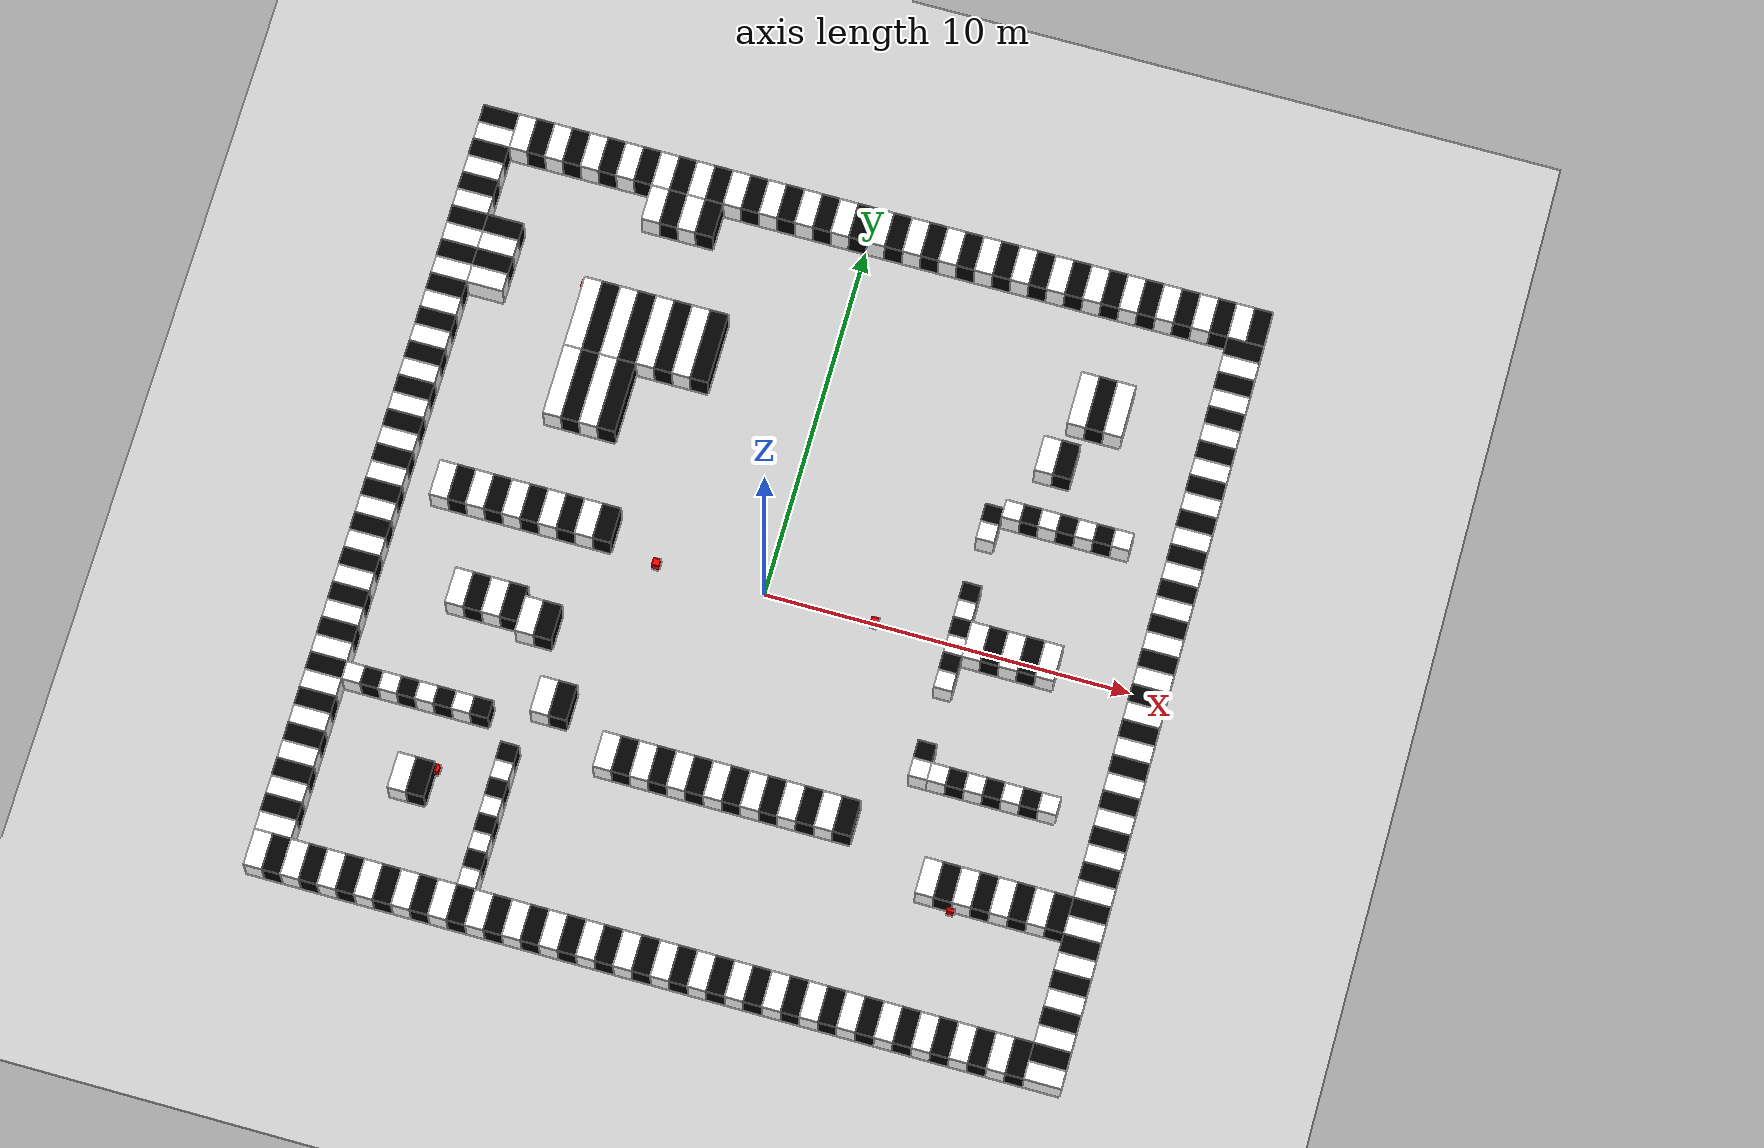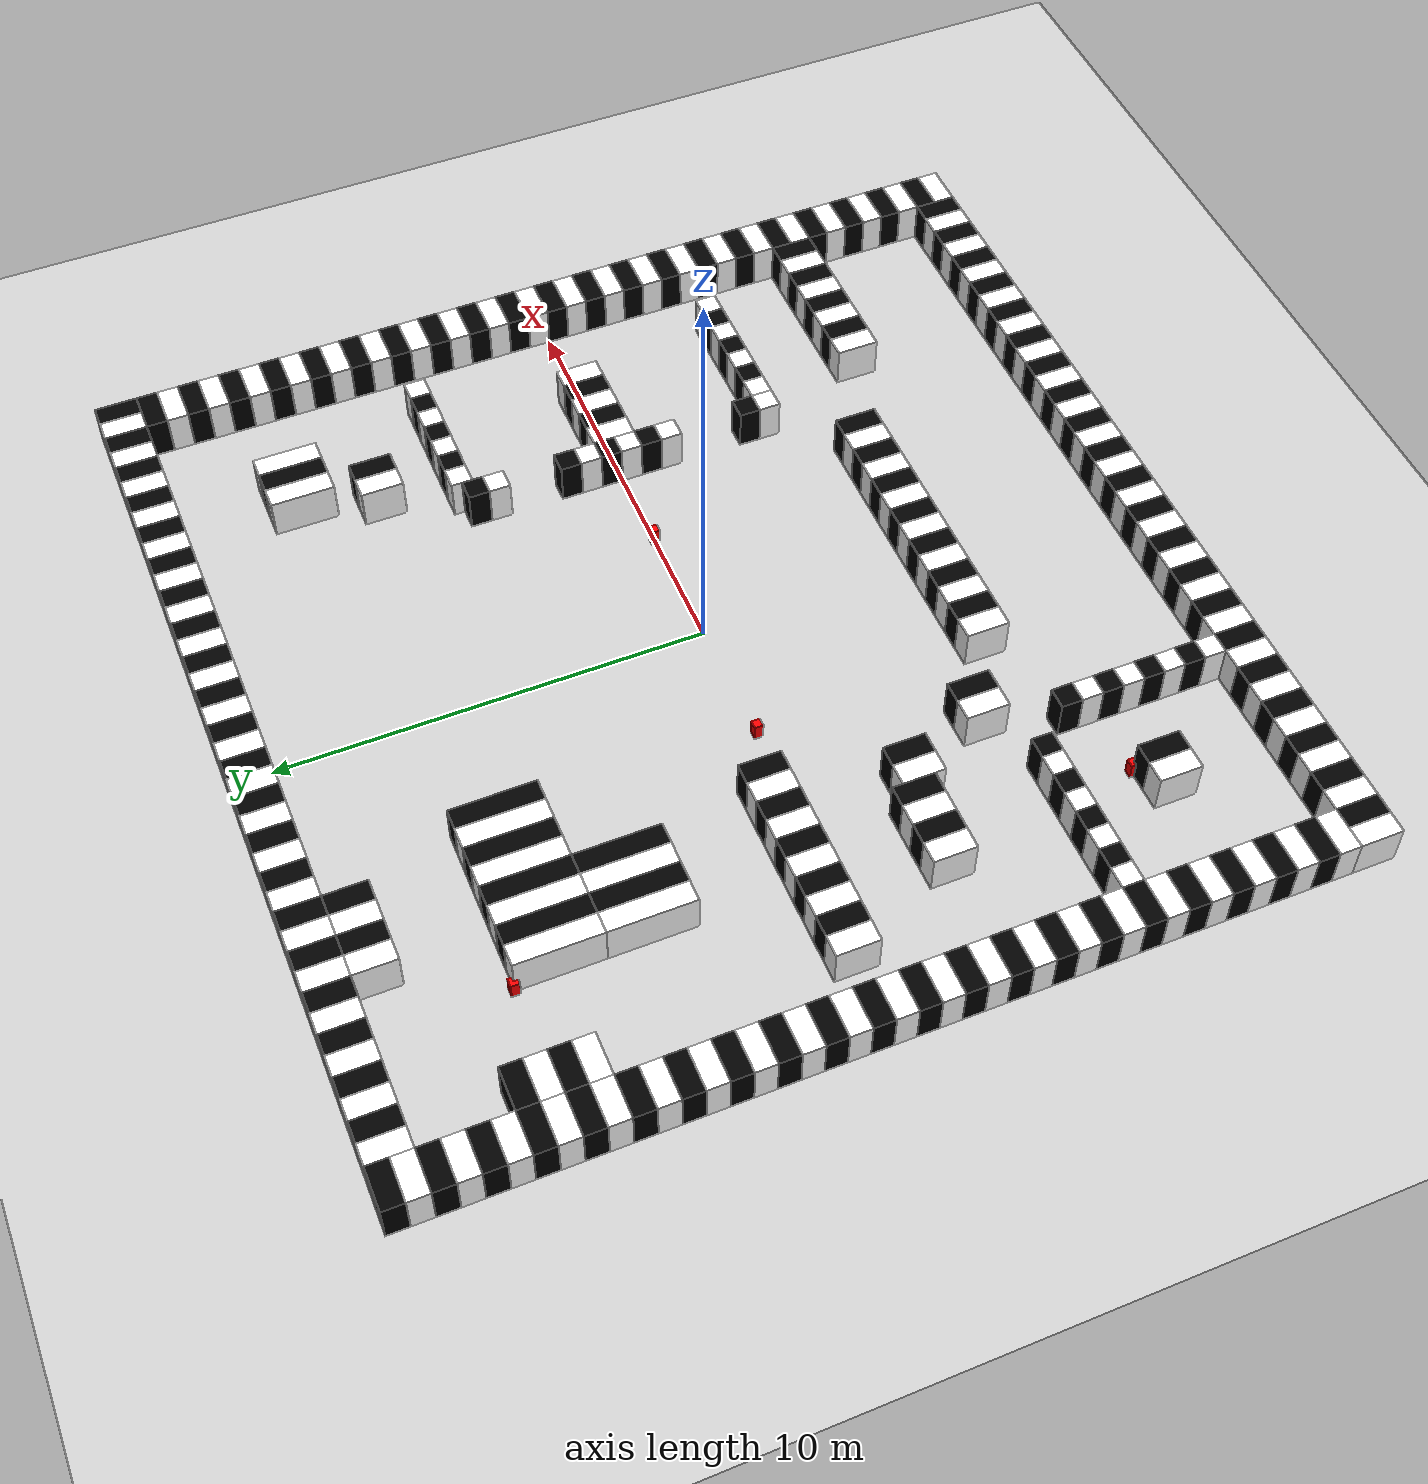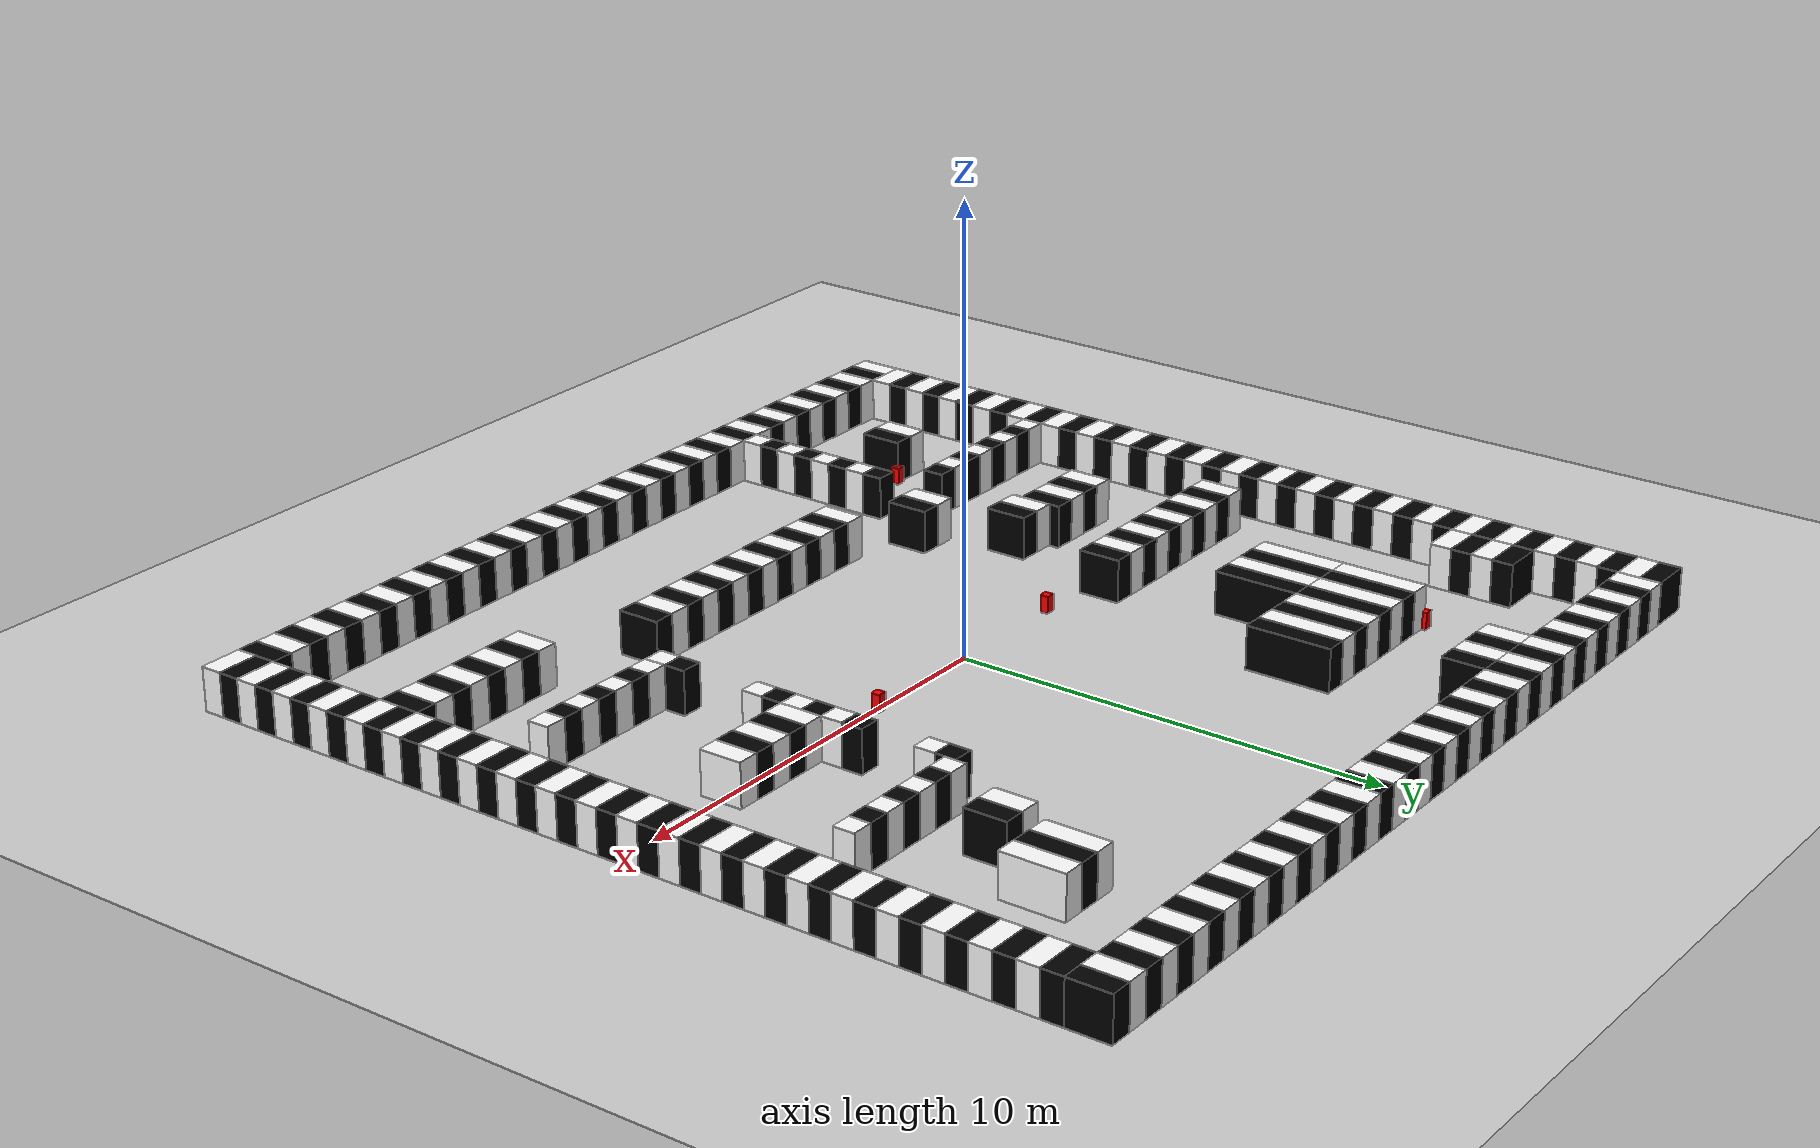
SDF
<sdf version="1.9">
 <world name="default">
  <plugin filename="gz-sim-physics-system" name="gz::sim::systems::Physics"/>
  <plugin filename="gz-sim-sensors-system" name="gz::sim::systems::Sensors">
   <render_engine>ogre2</render_engine>
  </plugin>
  <plugin filename="gz-sim-scene-broadcaster-system" name="gz::sim::systems::SceneBroadcaster"/>
  <plugin filename="gz-sim-user-commands-system" name="gz::sim::systems::UserCommands"/>
  <light name="directional_light" type="directional">
   <pose>0 0 10 0 0 0</pose>
   <diffuse>1 1 1 1</diffuse>
   <specular>0.1 0.1 0.1 1</specular>
   <direction>-0.5 0.1 -0.9</direction>
   <attenuation>
    <range>1000</range>
    <constant>0.9</constant>
    <linear>0.01</linear>
    <quadratic>0.001</quadratic>
   </attenuation>
  </light>
  <model name="ground_plane">
   <static>true</static>
   <link name="link">
    <collision name="collision">
     <geometry><plane><normal>0 0 1</normal><size>100 100</size></plane></geometry>
    </collision>
    <visual name="visual">
     <geometry><plane><normal>0 0 1</normal><size>100 100</size></plane></geometry>
     <material>
      <ambient>0.8 0.8 0.8 1</ambient>
      <diffuse>0.8 0.8 0.8 1</diffuse>
      <specular>0.8 0.8 0.8 1</specular>
     </material>
    </visual>
   </link>
  </model>
  <gravity>0 0 -9.8</gravity>
  <physics type="ode">
   <max_step_size>0.01</max_step_size>
   <real_time_factor>1</real_time_factor>
   <real_time_update_rate>100</real_time_update_rate>
  </physics>
  <model name="wall1">
   <static>true</static>
   <link name="link">
    <collision name="collision1">
     <geometry>
      <polyline>
       <point>10 10</point>
       <point>11 10</point>
       <point>11 -11</point>
       <point>10 -11</point>
       <height>1</height>
      </polyline>
     </geometry>
    </collision>
    <visual name="s1">
     <pose>10.5 -10.75 0.5 0 0 0</pose>
     <geometry><box><size>1 0.5 1</size></box></geometry>
     <material><ambient>1 1 1 1</ambient><diffuse>1 1 1 1</diffuse></material>
    </visual>
    <visual name="s2">
     <pose>10.5 -10.25 0.5 0 0 0</pose>
     <geometry><box><size>1 0.5 1</size></box></geometry>
     <material><ambient>0 0 0 1</ambient><diffuse>0 0 0 1</diffuse></material>
    </visual>
    <visual name="s3">
     <pose>10.5 -9.75 0.5 0 0 0</pose>
     <geometry><box><size>1 0.5 1</size></box></geometry>
     <material><ambient>1 1 1 1</ambient><diffuse>1 1 1 1</diffuse></material>
    </visual>
    <visual name="s4">
     <pose>10.5 -9.25 0.5 0 0 0</pose>
     <geometry><box><size>1 0.5 1</size></box></geometry>
     <material><ambient>0 0 0 1</ambient><diffuse>0 0 0 1</diffuse></material>
    </visual>
    <visual name="s5">
     <pose>10.5 -8.75 0.5 0 0 0</pose>
     <geometry><box><size>1 0.5 1</size></box></geometry>
     <material><ambient>1 1 1 1</ambient><diffuse>1 1 1 1</diffuse></material>
    </visual>
    <visual name="s6">
     <pose>10.5 -8.25 0.5 0 0 0</pose>
     <geometry><box><size>1 0.5 1</size></box></geometry>
     <material><ambient>0 0 0 1</ambient><diffuse>0 0 0 1</diffuse></material>
    </visual>
    <visual name="s7">
     <pose>10.5 -7.75 0.5 0 0 0</pose>
     <geometry><box><size>1 0.5 1</size></box></geometry>
     <material><ambient>1 1 1 1</ambient><diffuse>1 1 1 1</diffuse></material>
    </visual>
    <visual name="s8">
     <pose>10.5 -7.25 0.5 0 0 0</pose>
     <geometry><box><size>1 0.5 1</size></box></geometry>
     <material><ambient>0 0 0 1</ambient><diffuse>0 0 0 1</diffuse></material>
    </visual>
    <visual name="s9">
     <pose>10.5 -6.75 0.5 0 0 0</pose>
     <geometry><box><size>1 0.5 1</size></box></geometry>
     <material><ambient>1 1 1 1</ambient><diffuse>1 1 1 1</diffuse></material>
    </visual>
    <visual name="s10">
     <pose>10.5 -6.25 0.5 0 0 0</pose>
     <geometry><box><size>1 0.5 1</size></box></geometry>
     <material><ambient>0 0 0 1</ambient><diffuse>0 0 0 1</diffuse></material>
    </visual>
    <visual name="s11">
     <pose>10.5 -5.75 0.5 0 0 0</pose>
     <geometry><box><size>1 0.5 1</size></box></geometry>
     <material><ambient>1 1 1 1</ambient><diffuse>1 1 1 1</diffuse></material>
    </visual>
    <visual name="s12">
     <pose>10.5 -5.25 0.5 0 0 0</pose>
     <geometry><box><size>1 0.5 1</size></box></geometry>
     <material><ambient>0 0 0 1</ambient><diffuse>0 0 0 1</diffuse></material>
    </visual>
    <visual name="s13">
     <pose>10.5 -4.75 0.5 0 0 0</pose>
     <geometry><box><size>1 0.5 1</size></box></geometry>
     <material><ambient>1 1 1 1</ambient><diffuse>1 1 1 1</diffuse></material>
    </visual>
    <visual name="s14">
     <pose>10.5 -4.25 0.5 0 0 0</pose>
     <geometry><box><size>1 0.5 1</size></box></geometry>
     <material><ambient>0 0 0 1</ambient><diffuse>0 0 0 1</diffuse></material>
    </visual>
    <visual name="s15">
     <pose>10.5 -3.75 0.5 0 0 0</pose>
     <geometry><box><size>1 0.5 1</size></box></geometry>
     <material><ambient>1 1 1 1</ambient><diffuse>1 1 1 1</diffuse></material>
    </visual>
    <visual name="s16">
     <pose>10.5 -3.25 0.5 0 0 0</pose>
     <geometry><box><size>1 0.5 1</size></box></geometry>
     <material><ambient>0 0 0 1</ambient><diffuse>0 0 0 1</diffuse></material>
    </visual>
    <visual name="s17">
     <pose>10.5 -2.75 0.5 0 0 0</pose>
     <geometry><box><size>1 0.5 1</size></box></geometry>
     <material><ambient>1 1 1 1</ambient><diffuse>1 1 1 1</diffuse></material>
    </visual>
    <visual name="s18">
     <pose>10.5 -2.25 0.5 0 0 0</pose>
     <geometry><box><size>1 0.5 1</size></box></geometry>
     <material><ambient>0 0 0 1</ambient><diffuse>0 0 0 1</diffuse></material>
    </visual>
    <visual name="s19">
     <pose>10.5 -1.75 0.5 0 0 0</pose>
     <geometry><box><size>1 0.5 1</size></box></geometry>
     <material><ambient>1 1 1 1</ambient><diffuse>1 1 1 1</diffuse></material>
    </visual>
    <visual name="s20">
     <pose>10.5 -1.25 0.5 0 0 0</pose>
     <geometry><box><size>1 0.5 1</size></box></geometry>
     <material><ambient>0 0 0 1</ambient><diffuse>0 0 0 1</diffuse></material>
    </visual>
    <visual name="s21">
     <pose>10.5 -0.75 0.5 0 0 0</pose>
     <geometry><box><size>1 0.5 1</size></box></geometry>
     <material><ambient>1 1 1 1</ambient><diffuse>1 1 1 1</diffuse></material>
    </visual>
    <visual name="s22">
     <pose>10.5 -0.25 0.5 0 0 0</pose>
     <geometry><box><size>1 0.5 1</size></box></geometry>
     <material><ambient>0 0 0 1</ambient><diffuse>0 0 0 1</diffuse></material>
    </visual>
    <visual name="s23">
     <pose>10.5 0.25 0.5 0 0 0</pose>
     <geometry><box><size>1 0.5 1</size></box></geometry>
     <material><ambient>1 1 1 1</ambient><diffuse>1 1 1 1</diffuse></material>
    </visual>
    <visual name="s24">
     <pose>10.5 0.75 0.5 0 0 0</pose>
     <geometry><box><size>1 0.5 1</size></box></geometry>
     <material><ambient>0 0 0 1</ambient><diffuse>0 0 0 1</diffuse></material>
    </visual>
    <visual name="s25">
     <pose>10.5 1.25 0.5 0 0 0</pose>
     <geometry><box><size>1 0.5 1</size></box></geometry>
     <material><ambient>1 1 1 1</ambient><diffuse>1 1 1 1</diffuse></material>
    </visual>
    <visual name="s26">
     <pose>10.5 1.75 0.5 0 0 0</pose>
     <geometry><box><size>1 0.5 1</size></box></geometry>
     <material><ambient>0 0 0 1</ambient><diffuse>0 0 0 1</diffuse></material>
    </visual>
    <visual name="s27">
     <pose>10.5 2.25 0.5 0 0 0</pose>
     <geometry><box><size>1 0.5 1</size></box></geometry>
     <material><ambient>1 1 1 1</ambient><diffuse>1 1 1 1</diffuse></material>
    </visual>
    <visual name="s28">
     <pose>10.5 2.75 0.5 0 0 0</pose>
     <geometry><box><size>1 0.5 1</size></box></geometry>
     <material><ambient>0 0 0 1</ambient><diffuse>0 0 0 1</diffuse></material>
    </visual>
    <visual name="s29">
     <pose>10.5 3.25 0.5 0 0 0</pose>
     <geometry><box><size>1 0.5 1</size></box></geometry>
     <material><ambient>1 1 1 1</ambient><diffuse>1 1 1 1</diffuse></material>
    </visual>
    <visual name="s30">
     <pose>10.5 3.75 0.5 0 0 0</pose>
     <geometry><box><size>1 0.5 1</size></box></geometry>
     <material><ambient>0 0 0 1</ambient><diffuse>0 0 0 1</diffuse></material>
    </visual>
    <visual name="s31">
     <pose>10.5 4.25 0.5 0 0 0</pose>
     <geometry><box><size>1 0.5 1</size></box></geometry>
     <material><ambient>1 1 1 1</ambient><diffuse>1 1 1 1</diffuse></material>
    </visual>
    <visual name="s32">
     <pose>10.5 4.75 0.5 0 0 0</pose>
     <geometry><box><size>1 0.5 1</size></box></geometry>
     <material><ambient>0 0 0 1</ambient><diffuse>0 0 0 1</diffuse></material>
    </visual>
    <visual name="s33">
     <pose>10.5 5.25 0.5 0 0 0</pose>
     <geometry><box><size>1 0.5 1</size></box></geometry>
     <material><ambient>1 1 1 1</ambient><diffuse>1 1 1 1</diffuse></material>
    </visual>
    <visual name="s34">
     <pose>10.5 5.75 0.5 0 0 0</pose>
     <geometry><box><size>1 0.5 1</size></box></geometry>
     <material><ambient>0 0 0 1</ambient><diffuse>0 0 0 1</diffuse></material>
    </visual>
    <visual name="s35">
     <pose>10.5 6.25 0.5 0 0 0</pose>
     <geometry><box><size>1 0.5 1</size></box></geometry>
     <material><ambient>1 1 1 1</ambient><diffuse>1 1 1 1</diffuse></material>
    </visual>
    <visual name="s36">
     <pose>10.5 6.75 0.5 0 0 0</pose>
     <geometry><box><size>1 0.5 1</size></box></geometry>
     <material><ambient>0 0 0 1</ambient><diffuse>0 0 0 1</diffuse></material>
    </visual>
    <visual name="s37">
     <pose>10.5 7.25 0.5 0 0 0</pose>
     <geometry><box><size>1 0.5 1</size></box></geometry>
     <material><ambient>1 1 1 1</ambient><diffuse>1 1 1 1</diffuse></material>
    </visual>
    <visual name="s38">
     <pose>10.5 7.75 0.5 0 0 0</pose>
     <geometry><box><size>1 0.5 1</size></box></geometry>
     <material><ambient>0 0 0 1</ambient><diffuse>0 0 0 1</diffuse></material>
    </visual>
    <visual name="s39">
     <pose>10.5 8.25 0.5 0 0 0</pose>
     <geometry><box><size>1 0.5 1</size></box></geometry>
     <material><ambient>1 1 1 1</ambient><diffuse>1 1 1 1</diffuse></material>
    </visual>
    <visual name="s40">
     <pose>10.5 8.75 0.5 0 0 0</pose>
     <geometry><box><size>1 0.5 1</size></box></geometry>
     <material><ambient>0 0 0 1</ambient><diffuse>0 0 0 1</diffuse></material>
    </visual>
    <visual name="s41">
     <pose>10.5 9.25 0.5 0 0 0</pose>
     <geometry><box><size>1 0.5 1</size></box></geometry>
     <material><ambient>1 1 1 1</ambient><diffuse>1 1 1 1</diffuse></material>
    </visual>
    <visual name="s42">
     <pose>10.5 9.75 0.5 0 0 0</pose>
     <geometry><box><size>1 0.5 1</size></box></geometry>
     <material><ambient>0 0 0 1</ambient><diffuse>0 0 0 1</diffuse></material>
    </visual>
   </link>
  </model>
  <model name="wall2">
   <static>true</static>
   <link name="link">
    <collision name="collision1">
     <geometry>
      <polyline>
       <point>10 -10</point>
       <point>10 -11</point>
       <point>-11 -11</point>
       <point>-11 -10</point>
       <height>1</height>
      </polyline>
     </geometry>
    </collision>
    <visual name="s1">
     <pose>-10.75 -10.5 0.5 0 0 0</pose>
     <geometry><box><size>0.5 1 1</size></box></geometry>
     <material><ambient>1 1 1 1</ambient><diffuse>1 1 1 1</diffuse></material>
    </visual>
    <visual name="s2">
     <pose>-10.25 -10.5 0.5 0 0 0</pose>
     <geometry><box><size>0.5 1 1</size></box></geometry>
     <material><ambient>0 0 0 1</ambient><diffuse>0 0 0 1</diffuse></material>
    </visual>
    <visual name="s3">
     <pose>-9.75 -10.5 0.5 0 0 0</pose>
     <geometry><box><size>0.5 1 1</size></box></geometry>
     <material><ambient>1 1 1 1</ambient><diffuse>1 1 1 1</diffuse></material>
    </visual>
    <visual name="s4">
     <pose>-9.25 -10.5 0.5 0 0 0</pose>
     <geometry><box><size>0.5 1 1</size></box></geometry>
     <material><ambient>0 0 0 1</ambient><diffuse>0 0 0 1</diffuse></material>
    </visual>
    <visual name="s5">
     <pose>-8.75 -10.5 0.5 0 0 0</pose>
     <geometry><box><size>0.5 1 1</size></box></geometry>
     <material><ambient>1 1 1 1</ambient><diffuse>1 1 1 1</diffuse></material>
    </visual>
    <visual name="s6">
     <pose>-8.25 -10.5 0.5 0 0 0</pose>
     <geometry><box><size>0.5 1 1</size></box></geometry>
     <material><ambient>0 0 0 1</ambient><diffuse>0 0 0 1</diffuse></material>
    </visual>
    <visual name="s7">
     <pose>-7.75 -10.5 0.5 0 0 0</pose>
     <geometry><box><size>0.5 1 1</size></box></geometry>
     <material><ambient>1 1 1 1</ambient><diffuse>1 1 1 1</diffuse></material>
    </visual>
    <visual name="s8">
     <pose>-7.25 -10.5 0.5 0 0 0</pose>
     <geometry><box><size>0.5 1 1</size></box></geometry>
     <material><ambient>0 0 0 1</ambient><diffuse>0 0 0 1</diffuse></material>
    </visual>
    <visual name="s9">
     <pose>-6.75 -10.5 0.5 0 0 0</pose>
     <geometry><box><size>0.5 1 1</size></box></geometry>
     <material><ambient>1 1 1 1</ambient><diffuse>1 1 1 1</diffuse></material>
    </visual>
    <visual name="s10">
     <pose>-6.25 -10.5 0.5 0 0 0</pose>
     <geometry><box><size>0.5 1 1</size></box></geometry>
     <material><ambient>0 0 0 1</ambient><diffuse>0 0 0 1</diffuse></material>
    </visual>
    <visual name="s11">
     <pose>-5.75 -10.5 0.5 0 0 0</pose>
     <geometry><box><size>0.5 1 1</size></box></geometry>
     <material><ambient>1 1 1 1</ambient><diffuse>1 1 1 1</diffuse></material>
    </visual>
    <visual name="s12">
     <pose>-5.25 -10.5 0.5 0 0 0</pose>
     <geometry><box><size>0.5 1 1</size></box></geometry>
     <material><ambient>0 0 0 1</ambient><diffuse>0 0 0 1</diffuse></material>
    </visual>
    <visual name="s13">
     <pose>-4.75 -10.5 0.5 0 0 0</pose>
     <geometry><box><size>0.5 1 1</size></box></geometry>
     <material><ambient>1 1 1 1</ambient><diffuse>1 1 1 1</diffuse></material>
    </visual>
    <visual name="s14">
     <pose>-4.25 -10.5 0.5 0 0 0</pose>
     <geometry><box><size>0.5 1 1</size></box></geometry>
     <material><ambient>0 0 0 1</ambient><diffuse>0 0 0 1</diffuse></material>
    </visual>
    <visual name="s15">
     <pose>-3.75 -10.5 0.5 0 0 0</pose>
     <geometry><box><size>0.5 1 1</size></box></geometry>
     <material><ambient>1 1 1 1</ambient><diffuse>1 1 1 1</diffuse></material>
    </visual>
    <visual name="s16">
     <pose>-3.25 -10.5 0.5 0 0 0</pose>
     <geometry><box><size>0.5 1 1</size></box></geometry>
     <material><ambient>0 0 0 1</ambient><diffuse>0 0 0 1</diffuse></material>
    </visual>
    <visual name="s17">
     <pose>-2.75 -10.5 0.5 0 0 0</pose>
     <geometry><box><size>0.5 1 1</size></box></geometry>
     <material><ambient>1 1 1 1</ambient><diffuse>1 1 1 1</diffuse></material>
    </visual>
    <visual name="s18">
     <pose>-2.25 -10.5 0.5 0 0 0</pose>
     <geometry><box><size>0.5 1 1</size></box></geometry>
     <material><ambient>0 0 0 1</ambient><diffuse>0 0 0 1</diffuse></material>
    </visual>
    <visual name="s19">
     <pose>-1.75 -10.5 0.5 0 0 0</pose>
     <geometry><box><size>0.5 1 1</size></box></geometry>
     <material><ambient>1 1 1 1</ambient><diffuse>1 1 1 1</diffuse></material>
    </visual>
    <visual name="s20">
     <pose>-1.25 -10.5 0.5 0 0 0</pose>
     <geometry><box><size>0.5 1 1</size></box></geometry>
     <material><ambient>0 0 0 1</ambient><diffuse>0 0 0 1</diffuse></material>
    </visual>
    <visual name="s21">
     <pose>-0.75 -10.5 0.5 0 0 0</pose>
     <geometry><box><size>0.5 1 1</size></box></geometry>
     <material><ambient>1 1 1 1</ambient><diffuse>1 1 1 1</diffuse></material>
    </visual>
    <visual name="s22">
     <pose>-0.25 -10.5 0.5 0 0 0</pose>
     <geometry><box><size>0.5 1 1</size></box></geometry>
     <material><ambient>0 0 0 1</ambient><diffuse>0 0 0 1</diffuse></material>
    </visual>
    <visual name="s23">
     <pose>0.25 -10.5 0.5 0 0 0</pose>
     <geometry><box><size>0.5 1 1</size></box></geometry>
     <material><ambient>1 1 1 1</ambient><diffuse>1 1 1 1</diffuse></material>
    </visual>
    <visual name="s24">
     <pose>0.75 -10.5 0.5 0 0 0</pose>
     <geometry><box><size>0.5 1 1</size></box></geometry>
     <material><ambient>0 0 0 1</ambient><diffuse>0 0 0 1</diffuse></material>
    </visual>
    <visual name="s25">
     <pose>1.25 -10.5 0.5 0 0 0</pose>
     <geometry><box><size>0.5 1 1</size></box></geometry>
     <material><ambient>1 1 1 1</ambient><diffuse>1 1 1 1</diffuse></material>
    </visual>
    <visual name="s26">
     <pose>1.75 -10.5 0.5 0 0 0</pose>
     <geometry><box><size>0.5 1 1</size></box></geometry>
     <material><ambient>0 0 0 1</ambient><diffuse>0 0 0 1</diffuse></material>
    </visual>
    <visual name="s27">
     <pose>2.25 -10.5 0.5 0 0 0</pose>
     <geometry><box><size>0.5 1 1</size></box></geometry>
     <material><ambient>1 1 1 1</ambient><diffuse>1 1 1 1</diffuse></material>
    </visual>
    <visual name="s28">
     <pose>2.75 -10.5 0.5 0 0 0</pose>
     <geometry><box><size>0.5 1 1</size></box></geometry>
     <material><ambient>0 0 0 1</ambient><diffuse>0 0 0 1</diffuse></material>
    </visual>
    <visual name="s29">
     <pose>3.25 -10.5 0.5 0 0 0</pose>
     <geometry><box><size>0.5 1 1</size></box></geometry>
     <material><ambient>1 1 1 1</ambient><diffuse>1 1 1 1</diffuse></material>
    </visual>
    <visual name="s30">
     <pose>3.75 -10.5 0.5 0 0 0</pose>
     <geometry><box><size>0.5 1 1</size></box></geometry>
     <material><ambient>0 0 0 1</ambient><diffuse>0 0 0 1</diffuse></material>
    </visual>
    <visual name="s31">
     <pose>4.25 -10.5 0.5 0 0 0</pose>
     <geometry><box><size>0.5 1 1</size></box></geometry>
     <material><ambient>1 1 1 1</ambient><diffuse>1 1 1 1</diffuse></material>
    </visual>
    <visual name="s32">
     <pose>4.75 -10.5 0.5 0 0 0</pose>
     <geometry><box><size>0.5 1 1</size></box></geometry>
     <material><ambient>0 0 0 1</ambient><diffuse>0 0 0 1</diffuse></material>
    </visual>
    <visual name="s33">
     <pose>5.25 -10.5 0.5 0 0 0</pose>
     <geometry><box><size>0.5 1 1</size></box></geometry>
     <material><ambient>1 1 1 1</ambient><diffuse>1 1 1 1</diffuse></material>
    </visual>
    <visual name="s34">
     <pose>5.75 -10.5 0.5 0 0 0</pose>
     <geometry><box><size>0.5 1 1</size></box></geometry>
     <material><ambient>0 0 0 1</ambient><diffuse>0 0 0 1</diffuse></material>
    </visual>
    <visual name="s35">
     <pose>6.25 -10.5 0.5 0 0 0</pose>
     <geometry><box><size>0.5 1 1</size></box></geometry>
     <material><ambient>1 1 1 1</ambient><diffuse>1 1 1 1</diffuse></material>
    </visual>
    <visual name="s36">
     <pose>6.75 -10.5 0.5 0 0 0</pose>
     <geometry><box><size>0.5 1 1</size></box></geometry>
     <material><ambient>0 0 0 1</ambient><diffuse>0 0 0 1</diffuse></material>
    </visual>
    <visual name="s37">
     <pose>7.25 -10.5 0.5 0 0 0</pose>
     <geometry><box><size>0.5 1 1</size></box></geometry>
     <material><ambient>1 1 1 1</ambient><diffuse>1 1 1 1</diffuse></material>
    </visual>
    <visual name="s38">
     <pose>7.75 -10.5 0.5 0 0 0</pose>
     <geometry><box><size>0.5 1 1</size></box></geometry>
     <material><ambient>0 0 0 1</ambient><diffuse>0 0 0 1</diffuse></material>
    </visual>
    <visual name="s39">
     <pose>8.25 -10.5 0.5 0 0 0</pose>
     <geometry><box><size>0.5 1 1</size></box></geometry>
     <material><ambient>1 1 1 1</ambient><diffuse>1 1 1 1</diffuse></material>
    </visual>
    <visual name="s40">
     <pose>8.75 -10.5 0.5 0 0 0</pose>
     <geometry><box><size>0.5 1 1</size></box></geometry>
     <material><ambient>0 0 0 1</ambient><diffuse>0 0 0 1</diffuse></material>
    </visual>
    <visual name="s41">
     <pose>9.25 -10.5 0.5 0 0 0</pose>
     <geometry><box><size>0.5 1 1</size></box></geometry>
     <material><ambient>1 1 1 1</ambient><diffuse>1 1 1 1</diffuse></material>
    </visual>
    <visual name="s42">
     <pose>9.75 -10.5 0.5 0 0 0</pose>
     <geometry><box><size>0.5 1 1</size></box></geometry>
     <material><ambient>0 0 0 1</ambient><diffuse>0 0 0 1</diffuse></material>
    </visual>
   </link>
  </model>
  <model name="wall3">
   <static>true</static>
   <link name="link">
    <collision name="collision1">
     <geometry>
      <polyline>
       <point>-10 11</point>
       <point>-10 -10</point>
       <point>-11 -10</point>
       <point>-11 11</point>
       <height>1</height>
      </polyline>
     </geometry>
    </collision>
    <visual name="s1">
     <pose>-10.5 -9.75 0.5 0 0 0</pose>
     <geometry><box><size>1 0.5 1</size></box></geometry>
     <material><ambient>1 1 1 1</ambient><diffuse>1 1 1 1</diffuse></material>
    </visual>
    <visual name="s2">
     <pose>-10.5 -9.25 0.5 0 0 0</pose>
     <geometry><box><size>1 0.5 1</size></box></geometry>
     <material><ambient>0 0 0 1</ambient><diffuse>0 0 0 1</diffuse></material>
    </visual>
    <visual name="s3">
     <pose>-10.5 -8.75 0.5 0 0 0</pose>
     <geometry><box><size>1 0.5 1</size></box></geometry>
     <material><ambient>1 1 1 1</ambient><diffuse>1 1 1 1</diffuse></material>
    </visual>
    <visual name="s4">
     <pose>-10.5 -8.25 0.5 0 0 0</pose>
     <geometry><box><size>1 0.5 1</size></box></geometry>
     <material><ambient>0 0 0 1</ambient><diffuse>0 0 0 1</diffuse></material>
    </visual>
    <visual name="s5">
     <pose>-10.5 -7.75 0.5 0 0 0</pose>
     <geometry><box><size>1 0.5 1</size></box></geometry>
     <material><ambient>1 1 1 1</ambient><diffuse>1 1 1 1</diffuse></material>
    </visual>
    <visual name="s6">
     <pose>-10.5 -7.25 0.5 0 0 0</pose>
     <geometry><box><size>1 0.5 1</size></box></geometry>
     <material><ambient>0 0 0 1</ambient><diffuse>0 0 0 1</diffuse></material>
    </visual>
    <visual name="s7">
     <pose>-10.5 -6.75 0.5 0 0 0</pose>
     <geometry><box><size>1 0.5 1</size></box></geometry>
     <material><ambient>1 1 1 1</ambient><diffuse>1 1 1 1</diffuse></material>
    </visual>
    <visual name="s8">
     <pose>-10.5 -6.25 0.5 0 0 0</pose>
     <geometry><box><size>1 0.5 1</size></box></geometry>
     <material><ambient>0 0 0 1</ambient><diffuse>0 0 0 1</diffuse></material>
    </visual>
    <visual name="s9">
     <pose>-10.5 -5.75 0.5 0 0 0</pose>
     <geometry><box><size>1 0.5 1</size></box></geometry>
     <material><ambient>1 1 1 1</ambient><diffuse>1 1 1 1</diffuse></material>
    </visual>
    <visual name="s10">
     <pose>-10.5 -5.25 0.5 0 0 0</pose>
     <geometry><box><size>1 0.5 1</size></box></geometry>
     <material><ambient>0 0 0 1</ambient><diffuse>0 0 0 1</diffuse></material>
    </visual>
    <visual name="s11">
     <pose>-10.5 -4.75 0.5 0 0 0</pose>
     <geometry><box><size>1 0.5 1</size></box></geometry>
     <material><ambient>1 1 1 1</ambient><diffuse>1 1 1 1</diffuse></material>
    </visual>
    <visual name="s12">
     <pose>-10.5 -4.25 0.5 0 0 0</pose>
     <geometry><box><size>1 0.5 1</size></box></geometry>
     <material><ambient>0 0 0 1</ambient><diffuse>0 0 0 1</diffuse></material>
    </visual>
    <visual name="s13">
     <pose>-10.5 -3.75 0.5 0 0 0</pose>
     <geometry><box><size>1 0.5 1</size></box></geometry>
     <material><ambient>1 1 1 1</ambient><diffuse>1 1 1 1</diffuse></material>
    </visual>
    <visual name="s14">
     <pose>-10.5 -3.25 0.5 0 0 0</pose>
     <geometry><box><size>1 0.5 1</size></box></geometry>
     <material><ambient>0 0 0 1</ambient><diffuse>0 0 0 1</diffuse></material>
    </visual>
    <visual name="s15">
     <pose>-10.5 -2.75 0.5 0 0 0</pose>
     <geometry><box><size>1 0.5 1</size></box></geometry>
     <material><ambient>1 1 1 1</ambient><diffuse>1 1 1 1</diffuse></material>
    </visual>
    <visual name="s16">
     <pose>-10.5 -2.25 0.5 0 0 0</pose>
     <geometry><box><size>1 0.5 1</size></box></geometry>
     <material><ambient>0 0 0 1</ambient><diffuse>0 0 0 1</diffuse></material>
    </visual>
    <visual name="s17">
     <pose>-10.5 -1.75 0.5 0 0 0</pose>
     <geometry><box><size>1 0.5 1</size></box></geometry>
     <material><ambient>1 1 1 1</ambient><diffuse>1 1 1 1</diffuse></material>
    </visual>
    <visual name="s18">
     <pose>-10.5 -1.25 0.5 0 0 0</pose>
     <geometry><box><size>1 0.5 1</size></box></geometry>
     <material><ambient>0 0 0 1</ambient><diffuse>0 0 0 1</diffuse></material>
    </visual>
    <visual name="s19">
     <pose>-10.5 -0.75 0.5 0 0 0</pose>
     <geometry><box><size>1 0.5 1</size></box></geometry>
     <material><ambient>1 1 1 1</ambient><diffuse>1 1 1 1</diffuse></material>
    </visual>
    <visual name="s20">
     <pose>-10.5 -0.25 0.5 0 0 0</pose>
     <geometry><box><size>1 0.5 1</size></box></geometry>
     <material><ambient>0 0 0 1</ambient><diffuse>0 0 0 1</diffuse></material>
    </visual>
    <visual name="s21">
     <pose>-10.5 0.25 0.5 0 0 0</pose>
     <geometry><box><size>1 0.5 1</size></box></geometry>
     <material><ambient>1 1 1 1</ambient><diffuse>1 1 1 1</diffuse></material>
    </visual>
    <visual name="s22">
     <pose>-10.5 0.75 0.5 0 0 0</pose>
     <geometry><box><size>1 0.5 1</size></box></geometry>
     <material><ambient>0 0 0 1</ambient><diffuse>0 0 0 1</diffuse></material>
    </visual>
    <visual name="s23">
     <pose>-10.5 1.25 0.5 0 0 0</pose>
     <geometry><box><size>1 0.5 1</size></box></geometry>
     <material><ambient>1 1 1 1</ambient><diffuse>1 1 1 1</diffuse></material>
    </visual>
    <visual name="s24">
     <pose>-10.5 1.75 0.5 0 0 0</pose>
     <geometry><box><size>1 0.5 1</size></box></geometry>
     <material><ambient>0 0 0 1</ambient><diffuse>0 0 0 1</diffuse></material>
    </visual>
    <visual name="s25">
     <pose>-10.5 2.25 0.5 0 0 0</pose>
     <geometry><box><size>1 0.5 1</size></box></geometry>
     <material><ambient>1 1 1 1</ambient><diffuse>1 1 1 1</diffuse></material>
    </visual>
    <visual name="s26">
     <pose>-10.5 2.75 0.5 0 0 0</pose>
     <geometry><box><size>1 0.5 1</size></box></geometry>
     <material><ambient>0 0 0 1</ambient><diffuse>0 0 0 1</diffuse></material>
    </visual>
    <visual name="s27">
     <pose>-10.5 3.25 0.5 0 0 0</pose>
     <geometry><box><size>1 0.5 1</size></box></geometry>
     <material><ambient>1 1 1 1</ambient><diffuse>1 1 1 1</diffuse></material>
    </visual>
    <visual name="s28">
     <pose>-10.5 3.75 0.5 0 0 0</pose>
     <geometry><box><size>1 0.5 1</size></box></geometry>
     <material><ambient>0 0 0 1</ambient><diffuse>0 0 0 1</diffuse></material>
    </visual>
    <visual name="s29">
     <pose>-10.5 4.25 0.5 0 0 0</pose>
     <geometry><box><size>1 0.5 1</size></box></geometry>
     <material><ambient>1 1 1 1</ambient><diffuse>1 1 1 1</diffuse></material>
    </visual>
    <visual name="s30">
     <pose>-10.5 4.75 0.5 0 0 0</pose>
     <geometry><box><size>1 0.5 1</size></box></geometry>
     <material><ambient>0 0 0 1</ambient><diffuse>0 0 0 1</diffuse></material>
    </visual>
    <visual name="s31">
     <pose>-10.5 5.25 0.5 0 0 0</pose>
     <geometry><box><size>1 0.5 1</size></box></geometry>
     <material><ambient>1 1 1 1</ambient><diffuse>1 1 1 1</diffuse></material>
    </visual>
    <visual name="s32">
     <pose>-10.5 5.75 0.5 0 0 0</pose>
     <geometry><box><size>1 0.5 1</size></box></geometry>
     <material><ambient>0 0 0 1</ambient><diffuse>0 0 0 1</diffuse></material>
    </visual>
    <visual name="s33">
     <pose>-10.5 6.25 0.5 0 0 0</pose>
     <geometry><box><size>1 0.5 1</size></box></geometry>
     <material><ambient>1 1 1 1</ambient><diffuse>1 1 1 1</diffuse></material>
    </visual>
    <visual name="s34">
     <pose>-10.5 6.75 0.5 0 0 0</pose>
     <geometry><box><size>1 0.5 1</size></box></geometry>
     <material><ambient>0 0 0 1</ambient><diffuse>0 0 0 1</diffuse></material>
    </visual>
    <visual name="s35">
     <pose>-10.5 7.25 0.5 0 0 0</pose>
     <geometry><box><size>1 0.5 1</size></box></geometry>
     <material><ambient>1 1 1 1</ambient><diffuse>1 1 1 1</diffuse></material>
    </visual>
    <visual name="s36">
     <pose>-10.5 7.75 0.5 0 0 0</pose>
     <geometry><box><size>1 0.5 1</size></box></geometry>
     <material><ambient>0 0 0 1</ambient><diffuse>0 0 0 1</diffuse></material>
    </visual>
    <visual name="s37">
     <pose>-10.5 8.25 0.5 0 0 0</pose>
     <geometry><box><size>1 0.5 1</size></box></geometry>
     <material><ambient>1 1 1 1</ambient><diffuse>1 1 1 1</diffuse></material>
    </visual>
    <visual name="s38">
     <pose>-10.5 8.75 0.5 0 0 0</pose>
     <geometry><box><size>1 0.5 1</size></box></geometry>
     <material><ambient>0 0 0 1</ambient><diffuse>0 0 0 1</diffuse></material>
    </visual>
    <visual name="s39">
     <pose>-10.5 9.25 0.5 0 0 0</pose>
     <geometry><box><size>1 0.5 1</size></box></geometry>
     <material><ambient>1 1 1 1</ambient><diffuse>1 1 1 1</diffuse></material>
    </visual>
    <visual name="s40">
     <pose>-10.5 9.75 0.5 0 0 0</pose>
     <geometry><box><size>1 0.5 1</size></box></geometry>
     <material><ambient>0 0 0 1</ambient><diffuse>0 0 0 1</diffuse></material>
    </visual>
    <visual name="s41">
     <pose>-10.5 10.25 0.5 0 0 0</pose>
     <geometry><box><size>1 0.5 1</size></box></geometry>
     <material><ambient>1 1 1 1</ambient><diffuse>1 1 1 1</diffuse></material>
    </visual>
    <visual name="s42">
     <pose>-10.5 10.75 0.5 0 0 0</pose>
     <geometry><box><size>1 0.5 1</size></box></geometry>
     <material><ambient>0 0 0 1</ambient><diffuse>0 0 0 1</diffuse></material>
    </visual>
   </link>
  </model>
  <model name="wall4">
   <static>true</static>
   <link name="link">
    <collision name="collision1">
     <geometry>
      <polyline>
       <point>11 11</point>
       <point>11 10</point>
       <point>-10 10</point>
       <point>-10 11</point>
       <height>1</height>
      </polyline>
     </geometry>
    </collision>
    <visual name="s1">
     <pose>-9.75 10.5 0.5 0 0 0</pose>
     <geometry><box><size>0.5 1 1</size></box></geometry>
     <material><ambient>1 1 1 1</ambient><diffuse>1 1 1 1</diffuse></material>
    </visual>
    <visual name="s2">
     <pose>-9.25 10.5 0.5 0 0 0</pose>
     <geometry><box><size>0.5 1 1</size></box></geometry>
     <material><ambient>0 0 0 1</ambient><diffuse>0 0 0 1</diffuse></material>
    </visual>
    <visual name="s3">
     <pose>-8.75 10.5 0.5 0 0 0</pose>
     <geometry><box><size>0.5 1 1</size></box></geometry>
     <material><ambient>1 1 1 1</ambient><diffuse>1 1 1 1</diffuse></material>
    </visual>
    <visual name="s4">
     <pose>-8.25 10.5 0.5 0 0 0</pose>
     <geometry><box><size>0.5 1 1</size></box></geometry>
     <material><ambient>0 0 0 1</ambient><diffuse>0 0 0 1</diffuse></material>
    </visual>
    <visual name="s5">
     <pose>-7.75 10.5 0.5 0 0 0</pose>
     <geometry><box><size>0.5 1 1</size></box></geometry>
     <material><ambient>1 1 1 1</ambient><diffuse>1 1 1 1</diffuse></material>
    </visual>
    <visual name="s6">
     <pose>-7.25 10.5 0.5 0 0 0</pose>
     <geometry><box><size>0.5 1 1</size></box></geometry>
     <material><ambient>0 0 0 1</ambient><diffuse>0 0 0 1</diffuse></material>
    </visual>
    <visual name="s7">
     <pose>-6.75 10.5 0.5 0 0 0</pose>
     <geometry><box><size>0.5 1 1</size></box></geometry>
     <material><ambient>1 1 1 1</ambient><diffuse>1 1 1 1</diffuse></material>
    </visual>
    <visual name="s8">
     <pose>-6.25 10.5 0.5 0 0 0</pose>
     <geometry><box><size>0.5 1 1</size></box></geometry>
     <material><ambient>0 0 0 1</ambient><diffuse>0 0 0 1</diffuse></material>
    </visual>
    <visual name="s9">
     <pose>-5.75 10.5 0.5 0 0 0</pose>
     <geometry><box><size>0.5 1 1</size></box></geometry>
     <material><ambient>1 1 1 1</ambient><diffuse>1 1 1 1</diffuse></material>
    </visual>
    <visual name="s10">
     <pose>-5.25 10.5 0.5 0 0 0</pose>
     <geometry><box><size>0.5 1 1</size></box></geometry>
     <material><ambient>0 0 0 1</ambient><diffuse>0 0 0 1</diffuse></material>
    </visual>
    <visual name="s11">
     <pose>-4.75 10.5 0.5 0 0 0</pose>
     <geometry><box><size>0.5 1 1</size></box></geometry>
     <material><ambient>1 1 1 1</ambient><diffuse>1 1 1 1</diffuse></material>
    </visual>
    <visual name="s12">
     <pose>-4.25 10.5 0.5 0 0 0</pose>
     <geometry><box><size>0.5 1 1</size></box></geometry>
     <material><ambient>0 0 0 1</ambient><diffuse>0 0 0 1</diffuse></material>
    </visual>
    <visual name="s13">
     <pose>-3.75 10.5 0.5 0 0 0</pose>
     <geometry><box><size>0.5 1 1</size></box></geometry>
     <material><ambient>1 1 1 1</ambient><diffuse>1 1 1 1</diffuse></material>
    </visual>
    <visual name="s14">
     <pose>-3.25 10.5 0.5 0 0 0</pose>
     <geometry><box><size>0.5 1 1</size></box></geometry>
     <material><ambient>0 0 0 1</ambient><diffuse>0 0 0 1</diffuse></material>
    </visual>
    <visual name="s15">
     <pose>-2.75 10.5 0.5 0 0 0</pose>
     <geometry><box><size>0.5 1 1</size></box></geometry>
     <material><ambient>1 1 1 1</ambient><diffuse>1 1 1 1</diffuse></material>
    </visual>
    <visual name="s16">
     <pose>-2.25 10.5 0.5 0 0 0</pose>
     <geometry><box><size>0.5 1 1</size></box></geometry>
     <material><ambient>0 0 0 1</ambient><diffuse>0 0 0 1</diffuse></material>
    </visual>
    <visual name="s17">
     <pose>-1.75 10.5 0.5 0 0 0</pose>
     <geometry><box><size>0.5 1 1</size></box></geometry>
     <material><ambient>1 1 1 1</ambient><diffuse>1 1 1 1</diffuse></material>
    </visual>
    <visual name="s18">
     <pose>-1.25 10.5 0.5 0 0 0</pose>
     <geometry><box><size>0.5 1 1</size></box></geometry>
     <material><ambient>0 0 0 1</ambient><diffuse>0 0 0 1</diffuse></material>
    </visual>
    <visual name="s19">
     <pose>-0.75 10.5 0.5 0 0 0</pose>
     <geometry><box><size>0.5 1 1</size></box></geometry>
     <material><ambient>1 1 1 1</ambient><diffuse>1 1 1 1</diffuse></material>
    </visual>
    <visual name="s20">
     <pose>-0.25 10.5 0.5 0 0 0</pose>
     <geometry><box><size>0.5 1 1</size></box></geometry>
     <material><ambient>0 0 0 1</ambient><diffuse>0 0 0 1</diffuse></material>
    </visual>
    <visual name="s21">
     <pose>0.25 10.5 0.5 0 0 0</pose>
     <geometry><box><size>0.5 1 1</size></box></geometry>
     <material><ambient>1 1 1 1</ambient><diffuse>1 1 1 1</diffuse></material>
    </visual>
    <visual name="s22">
     <pose>0.75 10.5 0.5 0 0 0</pose>
     <geometry><box><size>0.5 1 1</size></box></geometry>
     <material><ambient>0 0 0 1</ambient><diffuse>0 0 0 1</diffuse></material>
    </visual>
    <visual name="s23">
     <pose>1.25 10.5 0.5 0 0 0</pose>
     <geometry><box><size>0.5 1 1</size></box></geometry>
     <material><ambient>1 1 1 1</ambient><diffuse>1 1 1 1</diffuse></material>
    </visual>
    <visual name="s24">
     <pose>1.75 10.5 0.5 0 0 0</pose>
     <geometry><box><size>0.5 1 1</size></box></geometry>
     <material><ambient>0 0 0 1</ambient><diffuse>0 0 0 1</diffuse></material>
    </visual>
    <visual name="s25">
     <pose>2.25 10.5 0.5 0 0 0</pose>
     <geometry><box><size>0.5 1 1</size></box></geometry>
     <material><ambient>1 1 1 1</ambient><diffuse>1 1 1 1</diffuse></material>
    </visual>
    <visual name="s26">
     <pose>2.75 10.5 0.5 0 0 0</pose>
     <geometry><box><size>0.5 1 1</size></box></geometry>
     <material><ambient>0 0 0 1</ambient><diffuse>0 0 0 1</diffuse></material>
    </visual>
    <visual name="s27">
     <pose>3.25 10.5 0.5 0 0 0</pose>
     <geometry><box><size>0.5 1 1</size></box></geometry>
     <material><ambient>1 1 1 1</ambient><diffuse>1 1 1 1</diffuse></material>
    </visual>
    <visual name="s28">
     <pose>3.75 10.5 0.5 0 0 0</pose>
     <geometry><box><size>0.5 1 1</size></box></geometry>
     <material><ambient>0 0 0 1</ambient><diffuse>0 0 0 1</diffuse></material>
    </visual>
    <visual name="s29">
     <pose>4.25 10.5 0.5 0 0 0</pose>
     <geometry><box><size>0.5 1 1</size></box></geometry>
     <material><ambient>1 1 1 1</ambient><diffuse>1 1 1 1</diffuse></material>
    </visual>
    <visual name="s30">
     <pose>4.75 10.5 0.5 0 0 0</pose>
     <geometry><box><size>0.5 1 1</size></box></geometry>
     <material><ambient>0 0 0 1</ambient><diffuse>0 0 0 1</diffuse></material>
    </visual>
    <visual name="s31">
     <pose>5.25 10.5 0.5 0 0 0</pose>
     <geometry><box><size>0.5 1 1</size></box></geometry>
     <material><ambient>1 1 1 1</ambient><diffuse>1 1 1 1</diffuse></material>
    </visual>
    <visual name="s32">
     <pose>5.75 10.5 0.5 0 0 0</pose>
     <geometry><box><size>0.5 1 1</size></box></geometry>
     <material><ambient>0 0 0 1</ambient><diffuse>0 0 0 1</diffuse></material>
    </visual>
    <visual name="s33">
     <pose>6.25 10.5 0.5 0 0 0</pose>
     <geometry><box><size>0.5 1 1</size></box></geometry>
     <material><ambient>1 1 1 1</ambient><diffuse>1 1 1 1</diffuse></material>
    </visual>
    <visual name="s34">
     <pose>6.75 10.5 0.5 0 0 0</pose>
     <geometry><box><size>0.5 1 1</size></box></geometry>
     <material><ambient>0 0 0 1</ambient><diffuse>0 0 0 1</diffuse></material>
    </visual>
    <visual name="s35">
     <pose>7.25 10.5 0.5 0 0 0</pose>
     <geometry><box><size>0.5 1 1</size></box></geometry>
     <material><ambient>1 1 1 1</ambient><diffuse>1 1 1 1</diffuse></material>
    </visual>
    <visual name="s36">
     <pose>7.75 10.5 0.5 0 0 0</pose>
     <geometry><box><size>0.5 1 1</size></box></geometry>
     <material><ambient>0 0 0 1</ambient><diffuse>0 0 0 1</diffuse></material>
    </visual>
    <visual name="s37">
     <pose>8.25 10.5 0.5 0 0 0</pose>
     <geometry><box><size>0.5 1 1</size></box></geometry>
     <material><ambient>1 1 1 1</ambient><diffuse>1 1 1 1</diffuse></material>
    </visual>
    <visual name="s38">
     <pose>8.75 10.5 0.5 0 0 0</pose>
     <geometry><box><size>0.5 1 1</size></box></geometry>
     <material><ambient>0 0 0 1</ambient><diffuse>0 0 0 1</diffuse></material>
    </visual>
    <visual name="s39">
     <pose>9.25 10.5 0.5 0 0 0</pose>
     <geometry><box><size>0.5 1 1</size></box></geometry>
     <material><ambient>1 1 1 1</ambient><diffuse>1 1 1 1</diffuse></material>
    </visual>
    <visual name="s40">
     <pose>9.75 10.5 0.5 0 0 0</pose>
     <geometry><box><size>0.5 1 1</size></box></geometry>
     <material><ambient>0 0 0 1</ambient><diffuse>0 0 0 1</diffuse></material>
    </visual>
    <visual name="s41">
     <pose>10.25 10.5 0.5 0 0 0</pose>
     <geometry><box><size>0.5 1 1</size></box></geometry>
     <material><ambient>1 1 1 1</ambient><diffuse>1 1 1 1</diffuse></material>
    </visual>
    <visual name="s42">
     <pose>10.75 10.5 0.5 0 0 0</pose>
     <geometry><box><size>0.5 1 1</size></box></geometry>
     <material><ambient>0 0 0 1</ambient><diffuse>0 0 0 1</diffuse></material>
    </visual>
   </link>
  </model>
  <model name="obs1">
   <static>true</static>
   <link name="link">
    <collision name="collision1">
     <geometry>
      <polyline>
       <point>-10 -5</point>
       <point>-6 -5</point>
       <point>-6 -5.5</point>
       <point>-10 -5.5</point>
       <height>1</height>
      </polyline>
     </geometry>
    </collision>
    <visual name="s1">
     <pose>-9.75 -5.25 0.5 0 0 0</pose>
     <geometry><box><size>0.5 0.5 1</size></box></geometry>
     <material><ambient>1 1 1 1</ambient><diffuse>1 1 1 1</diffuse></material>
    </visual>
    <visual name="s2">
     <pose>-9.25 -5.25 0.5 0 0 0</pose>
     <geometry><box><size>0.5 0.5 1</size></box></geometry>
     <material><ambient>0 0 0 1</ambient><diffuse>0 0 0 1</diffuse></material>
    </visual>
    <visual name="s3">
     <pose>-8.75 -5.25 0.5 0 0 0</pose>
     <geometry><box><size>0.5 0.5 1</size></box></geometry>
     <material><ambient>1 1 1 1</ambient><diffuse>1 1 1 1</diffuse></material>
    </visual>
    <visual name="s4">
     <pose>-8.25 -5.25 0.5 0 0 0</pose>
     <geometry><box><size>0.5 0.5 1</size></box></geometry>
     <material><ambient>0 0 0 1</ambient><diffuse>0 0 0 1</diffuse></material>
    </visual>
    <visual name="s5">
     <pose>-7.75 -5.25 0.5 0 0 0</pose>
     <geometry><box><size>0.5 0.5 1</size></box></geometry>
     <material><ambient>1 1 1 1</ambient><diffuse>1 1 1 1</diffuse></material>
    </visual>
    <visual name="s6">
     <pose>-7.25 -5.25 0.5 0 0 0</pose>
     <geometry><box><size>0.5 0.5 1</size></box></geometry>
     <material><ambient>0 0 0 1</ambient><diffuse>0 0 0 1</diffuse></material>
    </visual>
    <visual name="s7">
     <pose>-6.75 -5.25 0.5 0 0 0</pose>
     <geometry><box><size>0.5 0.5 1</size></box></geometry>
     <material><ambient>1 1 1 1</ambient><diffuse>1 1 1 1</diffuse></material>
    </visual>
    <visual name="s8">
     <pose>-6.25 -5.25 0.5 0 0 0</pose>
     <geometry><box><size>0.5 0.5 1</size></box></geometry>
     <material><ambient>0 0 0 1</ambient><diffuse>0 0 0 1</diffuse></material>
    </visual>
   </link>
  </model>
  <model name="obs2">
   <static>true</static>
   <link name="link">
    <collision name="collision1">
     <geometry>
      <polyline>
       <point>-5.5 -6</point>
       <point>-5 -6</point>
       <point>-5 -10</point>
       <point>-5.5 -10</point>
       <height>1</height>
      </polyline>
     </geometry>
    </collision>
    <visual name="s1">
     <pose>-5.25 -9.75 0.5 0 0 0</pose>
     <geometry><box><size>0.5 0.5 1</size></box></geometry>
     <material><ambient>1 1 1 1</ambient><diffuse>1 1 1 1</diffuse></material>
    </visual>
    <visual name="s2">
     <pose>-5.25 -9.25 0.5 0 0 0</pose>
     <geometry><box><size>0.5 0.5 1</size></box></geometry>
     <material><ambient>0 0 0 1</ambient><diffuse>0 0 0 1</diffuse></material>
    </visual>
    <visual name="s3">
     <pose>-5.25 -8.75 0.5 0 0 0</pose>
     <geometry><box><size>0.5 0.5 1</size></box></geometry>
     <material><ambient>1 1 1 1</ambient><diffuse>1 1 1 1</diffuse></material>
    </visual>
    <visual name="s4">
     <pose>-5.25 -8.25 0.5 0 0 0</pose>
     <geometry><box><size>0.5 0.5 1</size></box></geometry>
     <material><ambient>0 0 0 1</ambient><diffuse>0 0 0 1</diffuse></material>
    </visual>
    <visual name="s5">
     <pose>-5.25 -7.75 0.5 0 0 0</pose>
     <geometry><box><size>0.5 0.5 1</size></box></geometry>
     <material><ambient>1 1 1 1</ambient><diffuse>1 1 1 1</diffuse></material>
    </visual>
    <visual name="s6">
     <pose>-5.25 -7.25 0.5 0 0 0</pose>
     <geometry><box><size>0.5 0.5 1</size></box></geometry>
     <material><ambient>0 0 0 1</ambient><diffuse>0 0 0 1</diffuse></material>
    </visual>
    <visual name="s7">
     <pose>-5.25 -6.75 0.5 0 0 0</pose>
     <geometry><box><size>0.5 0.5 1</size></box></geometry>
     <material><ambient>1 1 1 1</ambient><diffuse>1 1 1 1</diffuse></material>
    </visual>
    <visual name="s8">
     <pose>-5.25 -6.25 0.5 0 0 0</pose>
     <geometry><box><size>0.5 0.5 1</size></box></geometry>
     <material><ambient>0 0 0 1</ambient><diffuse>0 0 0 1</diffuse></material>
    </visual>
   </link>
  </model>
  <model name="obs3">
   <static>true</static>
   <link name="link">
    <collision name="collision1">
     <geometry>
      <polyline>
       <point>-3 -5</point>
       <point>4 -5</point>
       <point>4 -6</point>
       <point>-3 -6</point>
       <height>1</height>
      </polyline>
     </geometry>
    </collision>
    <visual name="s1">
     <pose>-2.75 -5.5 0.5 0 0 0</pose>
     <geometry><box><size>0.5 1 1</size></box></geometry>
     <material><ambient>1 1 1 1</ambient><diffuse>1 1 1 1</diffuse></material>
    </visual>
    <visual name="s2">
     <pose>-2.25 -5.5 0.5 0 0 0</pose>
     <geometry><box><size>0.5 1 1</size></box></geometry>
     <material><ambient>0 0 0 1</ambient><diffuse>0 0 0 1</diffuse></material>
    </visual>
    <visual name="s3">
     <pose>-1.75 -5.5 0.5 0 0 0</pose>
     <geometry><box><size>0.5 1 1</size></box></geometry>
     <material><ambient>1 1 1 1</ambient><diffuse>1 1 1 1</diffuse></material>
    </visual>
    <visual name="s4">
     <pose>-1.25 -5.5 0.5 0 0 0</pose>
     <geometry><box><size>0.5 1 1</size></box></geometry>
     <material><ambient>0 0 0 1</ambient><diffuse>0 0 0 1</diffuse></material>
    </visual>
    <visual name="s5">
     <pose>-0.75 -5.5 0.5 0 0 0</pose>
     <geometry><box><size>0.5 1 1</size></box></geometry>
     <material><ambient>1 1 1 1</ambient><diffuse>1 1 1 1</diffuse></material>
    </visual>
    <visual name="s6">
     <pose>-0.25 -5.5 0.5 0 0 0</pose>
     <geometry><box><size>0.5 1 1</size></box></geometry>
     <material><ambient>0 0 0 1</ambient><diffuse>0 0 0 1</diffuse></material>
    </visual>
    <visual name="s7">
     <pose>0.25 -5.5 0.5 0 0 0</pose>
     <geometry><box><size>0.5 1 1</size></box></geometry>
     <material><ambient>1 1 1 1</ambient><diffuse>1 1 1 1</diffuse></material>
    </visual>
    <visual name="s8">
     <pose>0.75 -5.5 0.5 0 0 0</pose>
     <geometry><box><size>0.5 1 1</size></box></geometry>
     <material><ambient>0 0 0 1</ambient><diffuse>0 0 0 1</diffuse></material>
    </visual>
    <visual name="s9">
     <pose>1.25 -5.5 0.5 0 0 0</pose>
     <geometry><box><size>0.5 1 1</size></box></geometry>
     <material><ambient>1 1 1 1</ambient><diffuse>1 1 1 1</diffuse></material>
    </visual>
    <visual name="s10">
     <pose>1.75 -5.5 0.5 0 0 0</pose>
     <geometry><box><size>0.5 1 1</size></box></geometry>
     <material><ambient>0 0 0 1</ambient><diffuse>0 0 0 1</diffuse></material>
    </visual>
    <visual name="s11">
     <pose>2.25 -5.5 0.5 0 0 0</pose>
     <geometry><box><size>0.5 1 1</size></box></geometry>
     <material><ambient>1 1 1 1</ambient><diffuse>1 1 1 1</diffuse></material>
    </visual>
    <visual name="s12">
     <pose>2.75 -5.5 0.5 0 0 0</pose>
     <geometry><box><size>0.5 1 1</size></box></geometry>
     <material><ambient>0 0 0 1</ambient><diffuse>0 0 0 1</diffuse></material>
    </visual>
    <visual name="s13">
     <pose>3.25 -5.5 0.5 0 0 0</pose>
     <geometry><box><size>0.5 1 1</size></box></geometry>
     <material><ambient>1 1 1 1</ambient><diffuse>1 1 1 1</diffuse></material>
    </visual>
    <visual name="s14">
     <pose>3.75 -5.5 0.5 0 0 0</pose>
     <geometry><box><size>0.5 1 1</size></box></geometry>
     <material><ambient>0 0 0 1</ambient><diffuse>0 0 0 1</diffuse></material>
    </visual>
   </link>
  </model>
  <model name="obs4">
   <static>true</static>
   <link name="link">
    <collision name="collision1">
     <geometry>
      <polyline>
       <point>6 -6</point>
       <point>10 -6</point>
       <point>10 -7</point>
       <point>6 -7</point>
       <height>1</height>
      </polyline>
     </geometry>
    </collision>
    <visual name="s1">
     <pose>6.25 -6.5 0.5 0 0 0</pose>
     <geometry><box><size>0.5 1 1</size></box></geometry>
     <material><ambient>1 1 1 1</ambient><diffuse>1 1 1 1</diffuse></material>
    </visual>
    <visual name="s2">
     <pose>6.75 -6.5 0.5 0 0 0</pose>
     <geometry><box><size>0.5 1 1</size></box></geometry>
     <material><ambient>0 0 0 1</ambient><diffuse>0 0 0 1</diffuse></material>
    </visual>
    <visual name="s3">
     <pose>7.25 -6.5 0.5 0 0 0</pose>
     <geometry><box><size>0.5 1 1</size></box></geometry>
     <material><ambient>1 1 1 1</ambient><diffuse>1 1 1 1</diffuse></material>
    </visual>
    <visual name="s4">
     <pose>7.75 -6.5 0.5 0 0 0</pose>
     <geometry><box><size>0.5 1 1</size></box></geometry>
     <material><ambient>0 0 0 1</ambient><diffuse>0 0 0 1</diffuse></material>
    </visual>
    <visual name="s5">
     <pose>8.25 -6.5 0.5 0 0 0</pose>
     <geometry><box><size>0.5 1 1</size></box></geometry>
     <material><ambient>1 1 1 1</ambient><diffuse>1 1 1 1</diffuse></material>
    </visual>
    <visual name="s6">
     <pose>8.75 -6.5 0.5 0 0 0</pose>
     <geometry><box><size>0.5 1 1</size></box></geometry>
     <material><ambient>0 0 0 1</ambient><diffuse>0 0 0 1</diffuse></material>
    </visual>
    <visual name="s7">
     <pose>9.25 -6.5 0.5 0 0 0</pose>
     <geometry><box><size>0.5 1 1</size></box></geometry>
     <material><ambient>1 1 1 1</ambient><diffuse>1 1 1 1</diffuse></material>
    </visual>
    <visual name="s8">
     <pose>9.75 -6.5 0.5 0 0 0</pose>
     <geometry><box><size>0.5 1 1</size></box></geometry>
     <material><ambient>0 0 0 1</ambient><diffuse>0 0 0 1</diffuse></material>
    </visual>
   </link>
  </model>
  <model name="obs5">
   <static>true</static>
   <link name="link">
    <collision name="collision1">
     <geometry>
      <polyline>
       <point>-6 -2</point>
       <point>-5 -2</point>
       <point>-5 -3</point>
       <point>-6 -3</point>
       <height>1</height>
      </polyline>
     </geometry>
    </collision>
    <visual name="s1">
     <pose>-5.75 -2.5 0.5 0 0 0</pose>
     <geometry><box><size>0.5 1 1</size></box></geometry>
     <material><ambient>1 1 1 1</ambient><diffuse>1 1 1 1</diffuse></material>
    </visual>
    <visual name="s2">
     <pose>-5.25 -2.5 0.5 0 0 0</pose>
     <geometry><box><size>0.5 1 1</size></box></geometry>
     <material><ambient>0 0 0 1</ambient><diffuse>0 0 0 1</diffuse></material>
    </visual>
   </link>
  </model>
  <model name="obs6">
   <static>true</static>
   <link name="link">
    <collision name="collision1">
     <geometry>
      <polyline>
       <point>-9.25 1</point>
       <point>-4 1</point>
       <point>-4 0</point>
       <point>-9.25 0</point>
       <height>1</height>
      </polyline>
     </geometry>
    </collision>
    <visual name="s1">
     <pose>-9.0 0.5 0.5 0 0 0</pose>
     <geometry><box><size>0.5 1 1</size></box></geometry>
     <material><ambient>1 1 1 1</ambient><diffuse>1 1 1 1</diffuse></material>
    </visual>
    <visual name="s2">
     <pose>-8.5 0.5 0.5 0 0 0</pose>
     <geometry><box><size>0.5 1 1</size></box></geometry>
     <material><ambient>0 0 0 1</ambient><diffuse>0 0 0 1</diffuse></material>
    </visual>
    <visual name="s3">
     <pose>-8.0 0.5 0.5 0 0 0</pose>
     <geometry><box><size>0.5 1 1</size></box></geometry>
     <material><ambient>1 1 1 1</ambient><diffuse>1 1 1 1</diffuse></material>
    </visual>
    <visual name="s4">
     <pose>-7.5 0.5 0.5 0 0 0</pose>
     <geometry><box><size>0.5 1 1</size></box></geometry>
     <material><ambient>0 0 0 1</ambient><diffuse>0 0 0 1</diffuse></material>
    </visual>
    <visual name="s5">
     <pose>-7.0 0.5 0.5 0 0 0</pose>
     <geometry><box><size>0.5 1 1</size></box></geometry>
     <material><ambient>1 1 1 1</ambient><diffuse>1 1 1 1</diffuse></material>
    </visual>
    <visual name="s6">
     <pose>-6.5 0.5 0.5 0 0 0</pose>
     <geometry><box><size>0.5 1 1</size></box></geometry>
     <material><ambient>0 0 0 1</ambient><diffuse>0 0 0 1</diffuse></material>
    </visual>
    <visual name="s7">
     <pose>-6.0 0.5 0.5 0 0 0</pose>
     <geometry><box><size>0.5 1 1</size></box></geometry>
     <material><ambient>1 1 1 1</ambient><diffuse>1 1 1 1</diffuse></material>
    </visual>
    <visual name="s8">
     <pose>-5.5 0.5 0.5 0 0 0</pose>
     <geometry><box><size>0.5 1 1</size></box></geometry>
     <material><ambient>0 0 0 1</ambient><diffuse>0 0 0 1</diffuse></material>
    </visual>
    <visual name="s9">
     <pose>-5.0 0.5 0.5 0 0 0</pose>
     <geometry><box><size>0.5 1 1</size></box></geometry>
     <material><ambient>1 1 1 1</ambient><diffuse>1 1 1 1</diffuse></material>
    </visual>
    <visual name="s10">
     <pose>-4.5 0.5 0.5 0 0 0</pose>
     <geometry><box><size>0.5 1 1</size></box></geometry>
     <material><ambient>0 0 0 1</ambient><diffuse>0 0 0 1</diffuse></material>
    </visual>
   </link>
  </model>
  <model name="obs7">
   <static>true</static>
   <link name="link">
    <collision name="collision1">
     <geometry>
      <polyline>
       <point>-7 5</point>
       <point>-5 5</point>
       <point>-5 3</point>
       <point>-7 3</point>
       <height>1</height>
      </polyline>
     </geometry>
    </collision>
    <visual name="s1">
     <pose>-6.75 4 0.5 0 0 0</pose>
     <geometry><box><size>0.5 2 1</size></box></geometry>
     <material><ambient>1 1 1 1</ambient><diffuse>1 1 1 1</diffuse></material>
    </visual>
    <visual name="s2">
     <pose>-6.25 4 0.5 0 0 0</pose>
     <geometry><box><size>0.5 2 1</size></box></geometry>
     <material><ambient>0 0 0 1</ambient><diffuse>0 0 0 1</diffuse></material>
    </visual>
    <visual name="s3">
     <pose>-5.75 4 0.5 0 0 0</pose>
     <geometry><box><size>0.5 2 1</size></box></geometry>
     <material><ambient>1 1 1 1</ambient><diffuse>1 1 1 1</diffuse></material>
    </visual>
    <visual name="s4">
     <pose>-5.25 4 0.5 0 0 0</pose>
     <geometry><box><size>0.5 2 1</size></box></geometry>
     <material><ambient>0 0 0 1</ambient><diffuse>0 0 0 1</diffuse></material>
    </visual>
   </link>
  </model>
  <model name="obs8">
   <static>true</static>
   <link name="link">
    <collision name="collision1">
     <geometry>
      <polyline>
       <point>-7 7</point>
       <point>-3 7</point>
       <point>-3 5</point>
       <point>-7 5</point>
       <height>1</height>
      </polyline>
     </geometry>
    </collision>
    <visual name="s1">
     <pose>-6.75 6 0.5 0 0 0</pose>
     <geometry><box><size>0.5 2 1</size></box></geometry>
     <material><ambient>1 1 1 1</ambient><diffuse>1 1 1 1</diffuse></material>
    </visual>
    <visual name="s2">
     <pose>-6.25 6 0.5 0 0 0</pose>
     <geometry><box><size>0.5 2 1</size></box></geometry>
     <material><ambient>0 0 0 1</ambient><diffuse>0 0 0 1</diffuse></material>
    </visual>
    <visual name="s3">
     <pose>-5.75 6 0.5 0 0 0</pose>
     <geometry><box><size>0.5 2 1</size></box></geometry>
     <material><ambient>1 1 1 1</ambient><diffuse>1 1 1 1</diffuse></material>
    </visual>
    <visual name="s4">
     <pose>-5.25 6 0.5 0 0 0</pose>
     <geometry><box><size>0.5 2 1</size></box></geometry>
     <material><ambient>0 0 0 1</ambient><diffuse>0 0 0 1</diffuse></material>
    </visual>
    <visual name="s5">
     <pose>-4.75 6 0.5 0 0 0</pose>
     <geometry><box><size>0.5 2 1</size></box></geometry>
     <material><ambient>1 1 1 1</ambient><diffuse>1 1 1 1</diffuse></material>
    </visual>
    <visual name="s6">
     <pose>-4.25 6 0.5 0 0 0</pose>
     <geometry><box><size>0.5 2 1</size></box></geometry>
     <material><ambient>0 0 0 1</ambient><diffuse>0 0 0 1</diffuse></material>
    </visual>
    <visual name="s7">
     <pose>-3.75 6 0.5 0 0 0</pose>
     <geometry><box><size>0.5 2 1</size></box></geometry>
     <material><ambient>1 1 1 1</ambient><diffuse>1 1 1 1</diffuse></material>
    </visual>
    <visual name="s8">
     <pose>-3.25 6 0.5 0 0 0</pose>
     <geometry><box><size>0.5 2 1</size></box></geometry>
     <material><ambient>0 0 0 1</ambient><diffuse>0 0 0 1</diffuse></material>
    </visual>
   </link>
  </model>
  <model name="obs12">
   <static>true</static>
   <link name="link">
    <collision name="collision1">
     <geometry>
      <polyline>
       <point>6.5 8</point>
       <point>8 8</point>
       <point>8 6.5</point>
       <point>6.5 6.5</point>
       <height>1</height>
      </polyline>
     </geometry>
    </collision>
    <visual name="s1">
     <pose>6.75 7.25 0.5 0 0 0</pose>
     <geometry><box><size>0.5 1.5 1</size></box></geometry>
     <material><ambient>1 1 1 1</ambient><diffuse>1 1 1 1</diffuse></material>
    </visual>
    <visual name="s2">
     <pose>7.25 7.25 0.5 0 0 0</pose>
     <geometry><box><size>0.5 1.5 1</size></box></geometry>
     <material><ambient>0 0 0 1</ambient><diffuse>0 0 0 1</diffuse></material>
    </visual>
    <visual name="s3">
     <pose>7.75 7.25 0.5 0 0 0</pose>
     <geometry><box><size>0.5 1.5 1</size></box></geometry>
     <material><ambient>1 1 1 1</ambient><diffuse>1 1 1 1</diffuse></material>
    </visual>
   </link>
  </model>
  <model name="obs13">
   <static>true</static>
   <link name="link">
    <collision name="collision1">
     <geometry>
      <polyline>
       <point>6 6</point>
       <point>7 6</point>
       <point>7 5</point>
       <point>6 5</point>
       <height>1</height>
      </polyline>
     </geometry>
    </collision>
    <visual name="s1">
     <pose>6.25 5.5 0.5 0 0 0</pose>
     <geometry><box><size>0.5 1 1</size></box></geometry>
     <material><ambient>1 1 1 1</ambient><diffuse>1 1 1 1</diffuse></material>
    </visual>
    <visual name="s2">
     <pose>6.75 5.5 0.5 0 0 0</pose>
     <geometry><box><size>0.5 1 1</size></box></geometry>
     <material><ambient>0 0 0 1</ambient><diffuse>0 0 0 1</diffuse></material>
    </visual>
   </link>
  </model>
  <model name="obs14">
   <static>true</static>
   <link name="link">
    <collision name="collision1">
     <geometry>
      <polyline>
       <point>5 4</point>
       <point>5.5 4</point>
       <point>5.5 2.75</point>
       <point>5 2.75</point>
       <height>1</height>
      </polyline>
     </geometry>
    </collision>
    <visual name="s1">
     <pose>5.25 3.0 0.5 0 0 0</pose>
     <geometry><box><size>0.5 0.5 1</size></box></geometry>
     <material><ambient>1 1 1 1</ambient><diffuse>1 1 1 1</diffuse></material>
    </visual>
    <visual name="s2">
     <pose>5.25 3.5 0.5 0 0 0</pose>
     <geometry><box><size>0.5 0.5 1</size></box></geometry>
     <material><ambient>0 0 0 1</ambient><diffuse>0 0 0 1</diffuse></material>
    </visual>
   </link>
  </model>
  <model name="obs15">
   <static>true</static>
   <link name="link">
    <collision name="collision1">
     <geometry>
      <polyline>
       <point>5.5 4</point>
       <point>9 4</point>
       <point>9 3.5</point>
       <point>5.5 3.5</point>
       <height>1</height>
      </polyline>
     </geometry>
    </collision>
    <visual name="s1">
     <pose>5.75 3.75 0.5 0 0 0</pose>
     <geometry><box><size>0.5 0.5 1</size></box></geometry>
     <material><ambient>1 1 1 1</ambient><diffuse>1 1 1 1</diffuse></material>
    </visual>
    <visual name="s2">
     <pose>6.25 3.75 0.5 0 0 0</pose>
     <geometry><box><size>0.5 0.5 1</size></box></geometry>
     <material><ambient>0 0 0 1</ambient><diffuse>0 0 0 1</diffuse></material>
    </visual>
    <visual name="s3">
     <pose>6.75 3.75 0.5 0 0 0</pose>
     <geometry><box><size>0.5 0.5 1</size></box></geometry>
     <material><ambient>1 1 1 1</ambient><diffuse>1 1 1 1</diffuse></material>
    </visual>
    <visual name="s4">
     <pose>7.25 3.75 0.5 0 0 0</pose>
     <geometry><box><size>0.5 0.5 1</size></box></geometry>
     <material><ambient>0 0 0 1</ambient><diffuse>0 0 0 1</diffuse></material>
    </visual>
    <visual name="s5">
     <pose>7.75 3.75 0.5 0 0 0</pose>
     <geometry><box><size>0.5 0.5 1</size></box></geometry>
     <material><ambient>1 1 1 1</ambient><diffuse>1 1 1 1</diffuse></material>
    </visual>
    <visual name="s6">
     <pose>8.25 3.75 0.5 0 0 0</pose>
     <geometry><box><size>0.5 0.5 1</size></box></geometry>
     <material><ambient>0 0 0 1</ambient><diffuse>0 0 0 1</diffuse></material>
    </visual>
    <visual name="s7">
     <pose>8.75 3.75 0.5 0 0 0</pose>
     <geometry><box><size>0.5 0.5 1</size></box></geometry>
     <material><ambient>1 1 1 1</ambient><diffuse>1 1 1 1</diffuse></material>
    </visual>
   </link>
  </model>
  <model name="obs16">
   <static>true</static>
   <link name="link">
    <collision name="collision1">
     <geometry>
      <polyline>
       <point>5 1.5</point>
       <point>5.5 1.5</point>
       <point>5.5 -1.5</point>
       <point>5 -1.5</point>
       <height>1</height>
      </polyline>
     </geometry>
    </collision>
    <visual name="s1">
     <pose>5.25 -1.25 0.5 0 0 0</pose>
     <geometry><box><size>0.5 0.5 1</size></box></geometry>
     <material><ambient>1 1 1 1</ambient><diffuse>1 1 1 1</diffuse></material>
    </visual>
    <visual name="s2">
     <pose>5.25 -0.75 0.5 0 0 0</pose>
     <geometry><box><size>0.5 0.5 1</size></box></geometry>
     <material><ambient>0 0 0 1</ambient><diffuse>0 0 0 1</diffuse></material>
    </visual>
    <visual name="s3">
     <pose>5.25 -0.25 0.5 0 0 0</pose>
     <geometry><box><size>0.5 0.5 1</size></box></geometry>
     <material><ambient>1 1 1 1</ambient><diffuse>1 1 1 1</diffuse></material>
    </visual>
    <visual name="s4">
     <pose>5.25 0.25 0.5 0 0 0</pose>
     <geometry><box><size>0.5 0.5 1</size></box></geometry>
     <material><ambient>0 0 0 1</ambient><diffuse>0 0 0 1</diffuse></material>
    </visual>
    <visual name="s5">
     <pose>5.25 0.75 0.5 0 0 0</pose>
     <geometry><box><size>0.5 0.5 1</size></box></geometry>
     <material><ambient>1 1 1 1</ambient><diffuse>1 1 1 1</diffuse></material>
    </visual>
    <visual name="s6">
     <pose>5.25 1.25 0.5 0 0 0</pose>
     <geometry><box><size>0.5 0.5 1</size></box></geometry>
     <material><ambient>0 0 0 1</ambient><diffuse>0 0 0 1</diffuse></material>
    </visual>
   </link>
  </model>
  <model name="obs17">
   <static>true</static>
   <link name="link">
    <collision name="collision1">
     <geometry>
      <polyline>
       <point>5.5 0.5</point>
       <point>8 0.5</point>
       <point>8 -0.5</point>
       <point>5.5 -0.5</point>
       <height>1</height>
      </polyline>
     </geometry>
    </collision>
    <visual name="s1">
     <pose>5.75 0 0.5 0 0 0</pose>
     <geometry><box><size>0.5 1 1</size></box></geometry>
     <material><ambient>1 1 1 1</ambient><diffuse>1 1 1 1</diffuse></material>
    </visual>
    <visual name="s2">
     <pose>6.25 0 0.5 0 0 0</pose>
     <geometry><box><size>0.5 1 1</size></box></geometry>
     <material><ambient>0 0 0 1</ambient><diffuse>0 0 0 1</diffuse></material>
    </visual>
    <visual name="s3">
     <pose>6.75 0 0.5 0 0 0</pose>
     <geometry><box><size>0.5 1 1</size></box></geometry>
     <material><ambient>1 1 1 1</ambient><diffuse>1 1 1 1</diffuse></material>
    </visual>
    <visual name="s4">
     <pose>7.25 0 0.5 0 0 0</pose>
     <geometry><box><size>0.5 1 1</size></box></geometry>
     <material><ambient>0 0 0 1</ambient><diffuse>0 0 0 1</diffuse></material>
    </visual>
    <visual name="s5">
     <pose>7.75 0 0.5 0 0 0</pose>
     <geometry><box><size>0.5 1 1</size></box></geometry>
     <material><ambient>1 1 1 1</ambient><diffuse>1 1 1 1</diffuse></material>
    </visual>
   </link>
  </model>
  <model name="obs18">
   <static>true</static>
   <link name="link">
    <collision name="collision1">
     <geometry>
      <polyline>
       <point>5 -2.75</point>
       <point>5.5 -2.75</point>
       <point>5.5 -4</point>
       <point>5 -4</point>
       <height>1</height>
      </polyline>
     </geometry>
    </collision>
    <visual name="s1">
     <pose>5.25 -3.75 0.5 0 0 0</pose>
     <geometry><box><size>0.5 0.5 1</size></box></geometry>
     <material><ambient>1 1 1 1</ambient><diffuse>1 1 1 1</diffuse></material>
    </visual>
    <visual name="s2">
     <pose>5.25 -3.25 0.5 0 0 0</pose>
     <geometry><box><size>0.5 0.5 1</size></box></geometry>
     <material><ambient>0 0 0 1</ambient><diffuse>0 0 0 1</diffuse></material>
    </visual>
   </link>
  </model>
  <model name="obs19">
   <static>true</static>
   <link name="link">
    <collision name="collision1">
     <geometry>
      <polyline>
       <point>5.5 -3.5</point>
       <point>9 -3.5</point>
       <point>9 -4</point>
       <point>5.5 -4</point>
       <height>1</height>
      </polyline>
     </geometry>
    </collision>
    <visual name="s1">
     <pose>5.75 -3.75 0.5 0 0 0</pose>
     <geometry><box><size>0.5 0.5 1</size></box></geometry>
     <material><ambient>1 1 1 1</ambient><diffuse>1 1 1 1</diffuse></material>
    </visual>
    <visual name="s2">
     <pose>6.25 -3.75 0.5 0 0 0</pose>
     <geometry><box><size>0.5 0.5 1</size></box></geometry>
     <material><ambient>0 0 0 1</ambient><diffuse>0 0 0 1</diffuse></material>
    </visual>
    <visual name="s3">
     <pose>6.75 -3.75 0.5 0 0 0</pose>
     <geometry><box><size>0.5 0.5 1</size></box></geometry>
     <material><ambient>1 1 1 1</ambient><diffuse>1 1 1 1</diffuse></material>
    </visual>
    <visual name="s4">
     <pose>7.25 -3.75 0.5 0 0 0</pose>
     <geometry><box><size>0.5 0.5 1</size></box></geometry>
     <material><ambient>0 0 0 1</ambient><diffuse>0 0 0 1</diffuse></material>
    </visual>
    <visual name="s5">
     <pose>7.75 -3.75 0.5 0 0 0</pose>
     <geometry><box><size>0.5 0.5 1</size></box></geometry>
     <material><ambient>1 1 1 1</ambient><diffuse>1 1 1 1</diffuse></material>
    </visual>
    <visual name="s6">
     <pose>8.25 -3.75 0.5 0 0 0</pose>
     <geometry><box><size>0.5 0.5 1</size></box></geometry>
     <material><ambient>0 0 0 1</ambient><diffuse>0 0 0 1</diffuse></material>
    </visual>
    <visual name="s7">
     <pose>8.75 -3.75 0.5 0 0 0</pose>
     <geometry><box><size>0.5 0.5 1</size></box></geometry>
     <material><ambient>1 1 1 1</ambient><diffuse>1 1 1 1</diffuse></material>
    </visual>
   </link>
  </model>
  <model name="obs24">
   <static>true</static>
   <link name="link">
    <collision name="collision1">
     <geometry>
      <polyline>
       <point>-8 -7</point>
       <point>-7 -7</point>
       <point>-7 -8</point>
       <point>-8 -8</point>
       <height>1</height>
      </polyline>
     </geometry>
    </collision>
    <visual name="s1">
     <pose>-7.75 -7.5 0.5 0 0 0</pose>
     <geometry><box><size>0.5 1 1</size></box></geometry>
     <material><ambient>1 1 1 1</ambient><diffuse>1 1 1 1</diffuse></material>
    </visual>
    <visual name="s2">
     <pose>-7.25 -7.5 0.5 0 0 0</pose>
     <geometry><box><size>0.5 1 1</size></box></geometry>
     <material><ambient>0 0 0 1</ambient><diffuse>0 0 0 1</diffuse></material>
    </visual>
   </link>
  </model>
  <model name="obs25">
   <static>true</static>
   <link name="link">
    <collision name="collision1">
     <geometry>
      <polyline>
       <point>-8 -1.75</point>
       <point>-6 -1.75</point>
       <point>-6 -2.75</point>
       <point>-8 -2.75</point>
       <height>1</height>
      </polyline>
     </geometry>
    </collision>
    <visual name="s1">
     <pose>-7.75 -2.25 0.5 0 0 0</pose>
     <geometry><box><size>0.5 1 1</size></box></geometry>
     <material><ambient>1 1 1 1</ambient><diffuse>1 1 1 1</diffuse></material>
    </visual>
    <visual name="s2">
     <pose>-7.25 -2.25 0.5 0 0 0</pose>
     <geometry><box><size>0.5 1 1</size></box></geometry>
     <material><ambient>0 0 0 1</ambient><diffuse>0 0 0 1</diffuse></material>
    </visual>
    <visual name="s3">
     <pose>-6.75 -2.25 0.5 0 0 0</pose>
     <geometry><box><size>0.5 1 1</size></box></geometry>
     <material><ambient>1 1 1 1</ambient><diffuse>1 1 1 1</diffuse></material>
    </visual>
    <visual name="s4">
     <pose>-6.25 -2.25 0.5 0 0 0</pose>
     <geometry><box><size>0.5 1 1</size></box></geometry>
     <material><ambient>0 0 0 1</ambient><diffuse>0 0 0 1</diffuse></material>
    </visual>
   </link>
  </model>
  <model name="obs27">
   <static>true</static>
   <link name="link">
    <collision name="collision1">
     <geometry>
      <polyline>
       <point>-5 -4</point>
       <point>-4 -4</point>
       <point>-4 -5</point>
       <point>-5 -5</point>
       <height>1</height>
      </polyline>
     </geometry>
    </collision>
    <visual name="s1">
     <pose>-4.75 -4.5 0.5 0 0 0</pose>
     <geometry><box><size>0.5 1 1</size></box></geometry>
     <material><ambient>1 1 1 1</ambient><diffuse>1 1 1 1</diffuse></material>
    </visual>
    <visual name="s2">
     <pose>-4.25 -4.5 0.5 0 0 0</pose>
     <geometry><box><size>0.5 1 1</size></box></geometry>
     <material><ambient>0 0 0 1</ambient><diffuse>0 0 0 1</diffuse></material>
    </visual>
   </link>
  </model>
  <model name="obs29">
   <static>true</static>
   <link name="link">
    <collision name="collision1">
     <geometry>
      <polyline>
       <point>-10 8</point>
       <point>-9 8</point>
       <point>-9 6</point>
       <point>-10 6</point>
       <height>1</height>
      </polyline>
     </geometry>
    </collision>
    <visual name="s1">
     <pose>-9.5 6.25 0.5 0 0 0</pose>
     <geometry><box><size>1 0.5 1</size></box></geometry>
     <material><ambient>1 1 1 1</ambient><diffuse>1 1 1 1</diffuse></material>
    </visual>
    <visual name="s2">
     <pose>-9.5 6.75 0.5 0 0 0</pose>
     <geometry><box><size>1 0.5 1</size></box></geometry>
     <material><ambient>0 0 0 1</ambient><diffuse>0 0 0 1</diffuse></material>
    </visual>
    <visual name="s3">
     <pose>-9.5 7.25 0.5 0 0 0</pose>
     <geometry><box><size>1 0.5 1</size></box></geometry>
     <material><ambient>1 1 1 1</ambient><diffuse>1 1 1 1</diffuse></material>
    </visual>
    <visual name="s4">
     <pose>-9.5 7.75 0.5 0 0 0</pose>
     <geometry><box><size>1 0.5 1</size></box></geometry>
     <material><ambient>0 0 0 1</ambient><diffuse>0 0 0 1</diffuse></material>
    </visual>
   </link>
  </model>
  <model name="obs30">
   <static>true</static>
   <link name="link">
    <collision name="collision1">
     <geometry>
      <polyline>
       <point>-6 10</point>
       <point>-4 10</point>
       <point>-4 9</point>
       <point>-6 9</point>
       <height>1</height>
      </polyline>
     </geometry>
    </collision>
    <visual name="s1">
     <pose>-5.75 9.5 0.5 0 0 0</pose>
     <geometry><box><size>0.5 1 1</size></box></geometry>
     <material><ambient>1 1 1 1</ambient><diffuse>1 1 1 1</diffuse></material>
    </visual>
    <visual name="s2">
     <pose>-5.25 9.5 0.5 0 0 0</pose>
     <geometry><box><size>0.5 1 1</size></box></geometry>
     <material><ambient>0 0 0 1</ambient><diffuse>0 0 0 1</diffuse></material>
    </visual>
    <visual name="s3">
     <pose>-4.75 9.5 0.5 0 0 0</pose>
     <geometry><box><size>0.5 1 1</size></box></geometry>
     <material><ambient>1 1 1 1</ambient><diffuse>1 1 1 1</diffuse></material>
    </visual>
    <visual name="s4">
     <pose>-4.25 9.5 0.5 0 0 0</pose>
     <geometry><box><size>0.5 1 1</size></box></geometry>
     <material><ambient>0 0 0 1</ambient><diffuse>0 0 0 1</diffuse></material>
    </visual>
   </link>
  </model>
  <model name="eval_dyn1">
   <static>true</static>
   <pose>-7 7 0.2 0 0 0</pose>
   <link name="link">
    <collision name="collision"><geometry><box><size>0.2 0.2 0.4</size></box></geometry></collision>
    <visual name="visual">
     <geometry><box><size>0.2 0.2 0.4</size></box></geometry>
     <material><ambient>1 0 0 1</ambient><diffuse>1 0 0 1</diffuse></material>
    </visual>
   </link>
  </model>
  <model name="eval_dyn2">
   <static>true</static>
   <pose>7 7 0.2 0 0 0</pose>
   <link name="link">
    <collision name="collision"><geometry><box><size>0.2 0.2 0.4</size></box></geometry></collision>
    <visual name="visual">
     <geometry><box><size>0.2 0.2 0.4</size></box></geometry>
     <material><ambient>1 0 0 1</ambient><diffuse>1 0 0 1</diffuse></material>
    </visual>
   </link>
  </model>
  <model name="eval_dyn3">
   <static>true</static>
   <pose>-3 0 0.2 0 0 0</pose>
   <link name="link">
    <collision name="collision"><geometry><box><size>0.2 0.2 0.4</size></box></geometry></collision>
    <visual name="visual">
     <geometry><box><size>0.2 0.2 0.4</size></box></geometry>
     <material><ambient>1 0 0 1</ambient><diffuse>1 0 0 1</diffuse></material>
    </visual>
   </link>
  </model>
  <model name="eval_dyn4">
   <static>true</static>
   <pose>3 0 0.2 0 0 0</pose>
   <link name="link">
    <collision name="collision"><geometry><box><size>0.2 0.2 0.4</size></box></geometry></collision>
    <visual name="visual">
     <geometry><box><size>0.2 0.2 0.4</size></box></geometry>
     <material><ambient>1 0 0 1</ambient><diffuse>1 0 0 1</diffuse></material>
    </visual>
   </link>
  </model>
  <model name="eval_dyn5">
   <static>true</static>
   <pose>-7 -7 0.2 0 0 0</pose>
   <link name="link">
    <collision name="collision"><geometry><box><size>0.2 0.2 0.4</size></box></geometry></collision>
    <visual name="visual">
     <geometry><box><size>0.2 0.2 0.4</size></box></geometry>
     <material><ambient>1 0 0 1</ambient><diffuse>1 0 0 1</diffuse></material>
    </visual>
   </link>
  </model>
  <model name="eval_dyn6">
   <static>true</static>
   <pose>7 -7 0.2 0 0 0</pose>
   <link name="link">
    <collision name="collision"><geometry><box><size>0.2 0.2 0.4</size></box></geometry></collision>
    <visual name="visual">
     <geometry><box><size>0.2 0.2 0.4</size></box></geometry>
     <material><ambient>1 0 0 1</ambient><diffuse>1 0 0 1</diffuse></material>
    </visual>
   </link>
  </model>
 </world>
</sdf>
